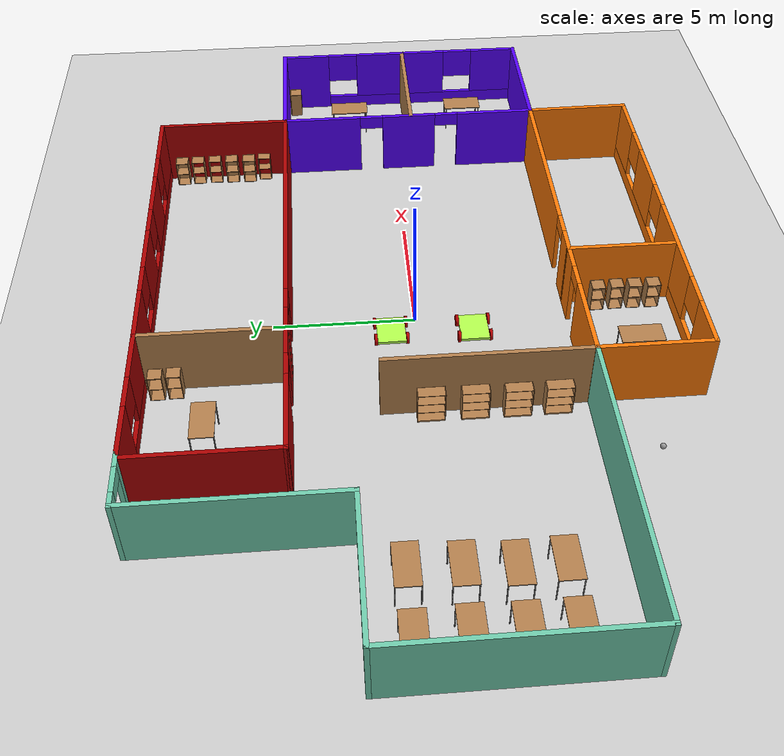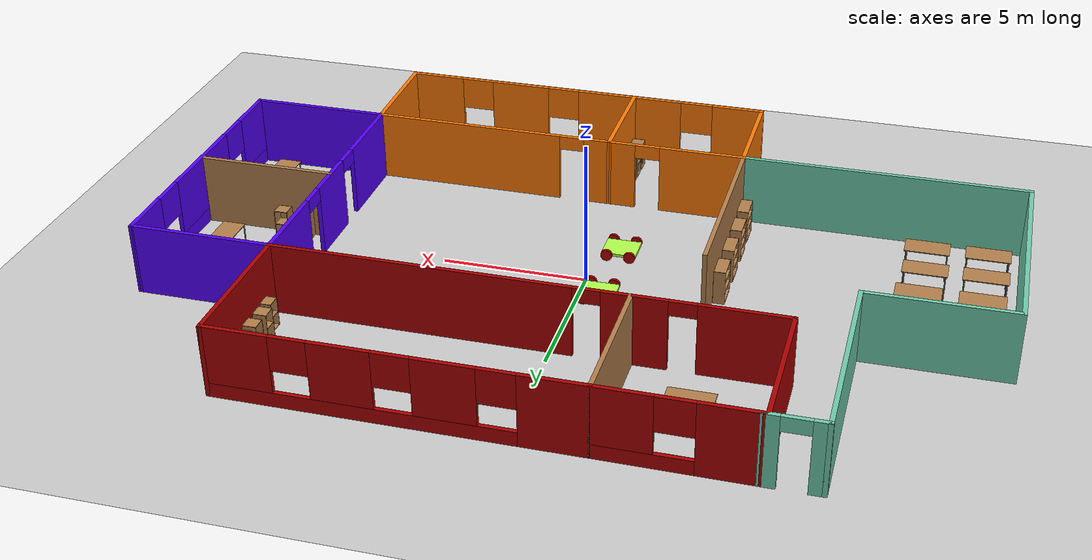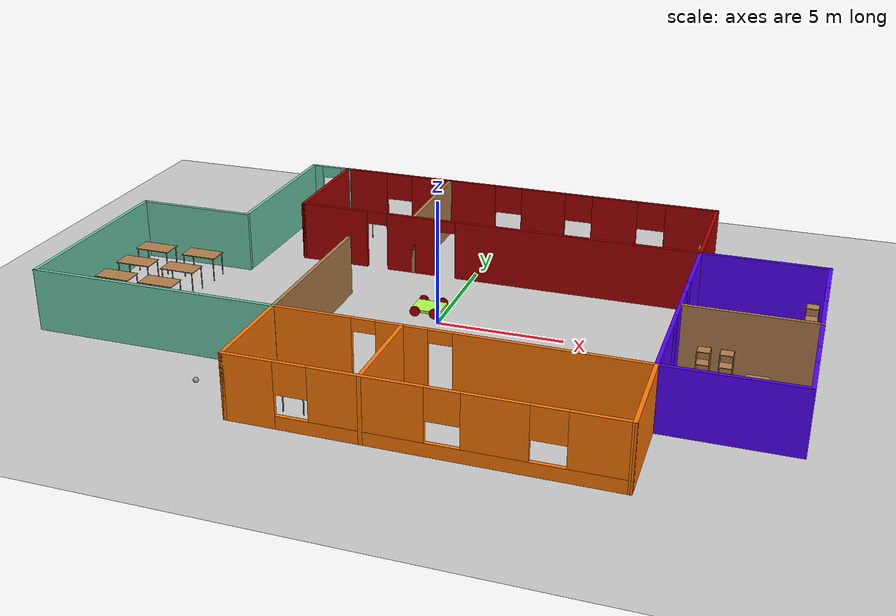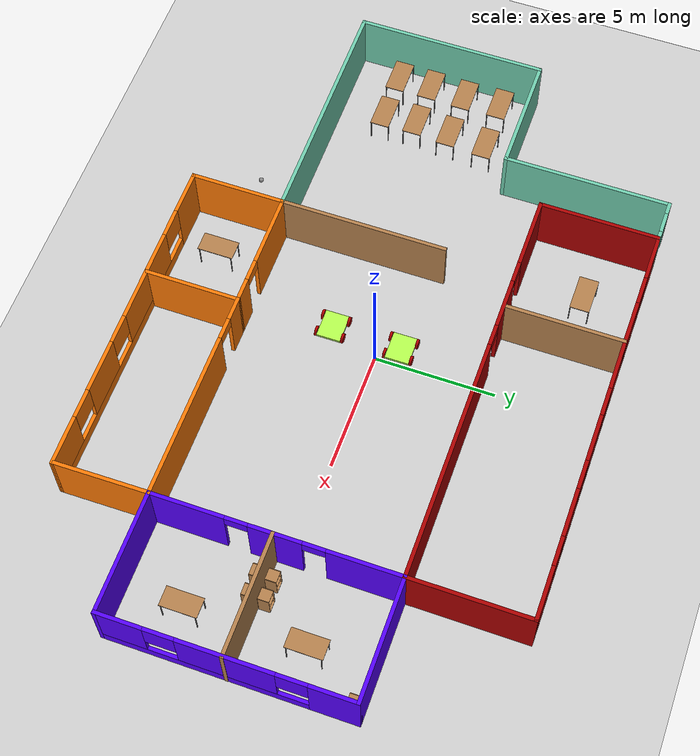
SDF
<sdf version="1.6">
 <world name="default">
  <plugin name="welcome" filename="libwelcome.so"/>
  <light name="sun" type="directional">
   <pose>0 0 10 0 -0 0</pose>
   <diffuse>0.8 0.8 0.8 1</diffuse>
   <specular>0.2 0.2 0.2 1</specular>
   <attenuation>
    <range>1000</range>
    <constant>0.9</constant>
    <linear>0.01</linear>
    <quadratic>0.001</quadratic>
   </attenuation>
   <direction>-0.5 0.1 -0.9</direction>
  </light>
  <model name="ground_plane">
   <static>1</static>
   <link name="link">
    <collision name="collision">
     <geometry><plane><normal>0 0 1</normal><size>100 100</size></plane></geometry>
     <surface>
      <contact><collide_bitmask>65535</collide_bitmask></contact>
      <friction><ode><mu>100</mu><mu2>50</mu2></ode></friction>
     </surface>
    </collision>
    <visual name="visual">
     <cast_shadows>0</cast_shadows>
     <geometry><plane><normal>0 0 1</normal><size>100 100</size></plane></geometry>
     <material>
      <script><uri>file://media/materials/scripts/gazebo.material</uri><name>Gazebo/Grey</name></script>
     </material>
    </visual>
   </link>
  </model>
  <gravity>0 0 -9.8</gravity>
  <magnetic_field>6e-06 2.3e-05 -4.2e-05</magnetic_field>
  <atmosphere type="adiabatic"/>
  <physics name="default_physics" default="0" type="ode">
   <max_step_size>0.001</max_step_size>
   <real_time_factor>1</real_time_factor>
   <real_time_update_rate>1000</real_time_update_rate>
  </physics>
  <scene><ambient>0.4 0.4 0.4 1</ambient><background>0.7 0.7 0.7 1</background><shadows>1</shadows></scene>
  <spherical_coordinates>
   <surface_model>EARTH_WGS84</surface_model>
   <latitude_deg>0</latitude_deg>
   <longitude_deg>0</longitude_deg>
   <elevation>0</elevation>
   <heading_deg>0</heading_deg>
  </spherical_coordinates>
  <model name="Building">
   <link name="Wall_10">
    <collision name="Wall_10_Collision">
     <geometry><box><size>5 0.15 2.5</size></box></geometry>
     <pose>0 0 1.25 0 -0 0</pose>
    </collision>
    <visual name="Wall_10_Visual">
     <pose>0 0 1.25 0 -0 0</pose>
     <geometry><box><size>5 0.15 2.5</size></box></geometry>
     <material>
      <script><uri>file://media/materials/scripts/gazebo.material</uri><name>Gazebo/Grey</name></script>
      <ambient>0.666667 0 0 1</ambient>
     </material>
     <meta><layer>0</layer></meta>
    </visual>
    <pose>9.27018 6.82319 0 0 0 -1.5708</pose>
   </link>
   <link name="Wall_11">
    <collision name="Wall_11_Collision">
     <geometry><box><size>5 0.15 2.5</size></box></geometry>
     <pose>0 0 1.25 0 -0 0</pose>
    </collision>
    <visual name="Wall_11_Visual">
     <pose>0 0 1.25 0 -0 0</pose>
     <geometry><box><size>5 0.15 2.5</size></box></geometry>
     <material>
      <script><uri>file://media/materials/scripts/gazebo.material</uri><name>Gazebo/Grey</name></script>
      <ambient>0.333333 0 1 1</ambient>
     </material>
     <meta><layer>0</layer></meta>
    </visual>
    <pose>11.6952 4.39843 0 0 -0 9.8e-05</pose>
   </link>
   <link name="Wall_12">
    <pose>14.1202 -0.52633 0 0 0 -1.5708</pose>
    <visual name="Wall_12_Visual_0">
     <pose>-4.03442 0 1.25 0 -0 0</pose>
     <geometry><box><size>1.93115 0.15 2.5</size></box></geometry>
     <material>
      <script><uri>file://media/materials/scripts/gazebo.material</uri><name>Gazebo/Grey</name></script>
      <ambient>0.333333 0 1 1</ambient>
     </material>
     <meta><layer>0</layer></meta>
    </visual>
    <collision name="Wall_12_Collision_0">
     <geometry><box><size>1.93115 0.15 2.5</size></box></geometry>
     <pose>-4.03442 0 1.25 0 -0 0</pose>
    </collision>
    <visual name="Wall_12_Visual_1">
     <pose>0.965577 0 0.25 0 -0 0</pose>
     <geometry><box><size>8.06885 0.15 0.5</size></box></geometry>
     <material>
      <script><uri>file://media/materials/scripts/gazebo.material</uri><name>Gazebo/Grey</name></script>
      <ambient>0.333333 0 1 1</ambient>
     </material>
     <meta><layer>0</layer></meta>
    </visual>
    <collision name="Wall_12_Collision_1">
     <geometry><box><size>8.06885 0.15 0.5</size></box></geometry>
     <pose>0.965577 0 0.25 0 -0 0</pose>
    </collision>
    <visual name="Wall_12_Visual_2">
     <pose>0.015256 0 1.5 0 -0 0</pose>
     <geometry><box><size>3.7682 0.15 2</size></box></geometry>
     <material>
      <script><uri>file://media/materials/scripts/gazebo.material</uri><name>Gazebo/Grey</name></script>
      <ambient>0.333333 0 1 1</ambient>
     </material>
     <meta><layer>0</layer></meta>
    </visual>
    <collision name="Wall_12_Collision_2">
     <geometry><box><size>3.7682 0.15 2</size></box></geometry>
     <pose>0.015256 0 1.5 0 -0 0</pose>
    </collision>
    <visual name="Wall_12_Visual_3">
     <pose>4.04968 0 1.5 0 -0 0</pose>
     <geometry><box><size>1.90064 0.15 2</size></box></geometry>
     <material>
      <script><uri>file://media/materials/scripts/gazebo.material</uri><name>Gazebo/Grey</name></script>
      <ambient>0.333333 0 1 1</ambient>
     </material>
     <meta><layer>0</layer></meta>
    </visual>
    <collision name="Wall_12_Collision_3">
     <geometry><box><size>1.90064 0.15 2</size></box></geometry>
     <pose>4.04968 0 1.5 0 -0 0</pose>
    </collision>
    <visual name="Wall_12_Visual_4">
     <pose>-2.46885 0 1.9 0 -0 0</pose>
     <geometry><box><size>1.2 0.15 1.2</size></box></geometry>
     <material>
      <script><uri>file://media/materials/scripts/gazebo.material</uri><name>Gazebo/Grey</name></script>
      <ambient>0.333333 0 1 1</ambient>
     </material>
     <meta><layer>0</layer></meta>
    </visual>
    <collision name="Wall_12_Collision_4">
     <geometry><box><size>1.2 0.15 1.2</size></box></geometry>
     <pose>-2.46885 0 1.9 0 -0 0</pose>
    </collision>
    <visual name="Wall_12_Visual_5">
     <pose>2.49936 0 1.9 0 -0 0</pose>
     <geometry><box><size>1.2 0.15 1.2</size></box></geometry>
     <material>
      <script><uri>file://media/materials/scripts/gazebo.material</uri><name>Gazebo/Grey</name></script>
      <ambient>0.333333 0 1 1</ambient>
     </material>
     <meta><layer>0</layer></meta>
    </visual>
    <collision name="Wall_12_Collision_5">
     <geometry><box><size>1.2 0.15 1.2</size></box></geometry>
     <pose>2.49936 0 1.9 0 -0 0</pose>
    </collision>
   </link>
   <link name="Wall_13">
    <collision name="Wall_13_Collision">
     <geometry><box><size>5 0.15 2.5</size></box></geometry>
     <pose>0 0 1.25 0 -0 0</pose>
    </collision>
    <visual name="Wall_13_Visual">
     <pose>0 0 1.25 0 -0 0</pose>
     <geometry><box><size>5 0.15 2.5</size></box></geometry>
     <material>
      <script><uri>file://media/materials/scripts/gazebo.material</uri><name>Gazebo/Grey</name></script>
      <ambient>0.333333 0 1 1</ambient>
     </material>
     <meta><layer>0</layer></meta>
    </visual>
    <pose>11.6952 -5.45133 0 0 -0 3.14159</pose>
   </link>
   <link name="Wall_15">
    <collision name="Wall_15_Collision">
     <geometry><box><size>5 0.15 2.5</size></box></geometry>
     <pose>0 0 1.25 0 -0 0</pose>
    </collision>
    <visual name="Wall_15_Visual">
     <pose>0 0 1.25 0 -0 0</pose>
     <geometry><box><size>5 0.15 2.5</size></box></geometry>
     <material>
      <script><uri>file://media/materials/scripts/gazebo.material</uri><name>Gazebo/Grey</name></script>
      <ambient>0.666667 0 0 1</ambient>
     </material>
     <meta><layer>0</layer></meta>
    </visual>
    <pose>-7.57982 6.82319 0 0 0 -1.5708</pose>
   </link>
   <link name="Wall_17">
    <pose>0.845177 4.39819 0 0 -0 0</pose>
    <visual name="Wall_17_Visual_0">
     <pose>-6.99749 0 1.25 0 -0 0</pose>
     <geometry><box><size>3.00503 0.15 2.5</size></box></geometry>
     <material>
      <script><uri>file://media/materials/scripts/gazebo.material</uri><name>Gazebo/Grey</name></script>
      <ambient>0.666667 0 0 1</ambient>
     </material>
     <meta><layer>0</layer></meta>
    </visual>
    <collision name="Wall_17_Collision_0">
     <geometry><box><size>3.00503 0.15 2.5</size></box></geometry>
     <pose>-6.99749 0 1.25 0 -0 0</pose>
    </collision>
    <visual name="Wall_17_Visual_1">
     <pose>-3.538 0 1.25 0 -0 0</pose>
     <geometry><box><size>2.11394 0.15 2.5</size></box></geometry>
     <material>
      <script><uri>file://media/materials/scripts/gazebo.material</uri><name>Gazebo/Grey</name></script>
      <ambient>0.666667 0 0 1</ambient>
     </material>
     <meta><layer>0</layer></meta>
    </visual>
    <collision name="Wall_17_Collision_1">
     <geometry><box><size>2.11394 0.15 2.5</size></box></geometry>
     <pose>-3.538 0 1.25 0 -0 0</pose>
    </collision>
    <visual name="Wall_17_Visual_2">
     <pose>3.45948 0 1.25 0 -0 0</pose>
     <geometry><box><size>10.081 0.15 2.5</size></box></geometry>
     <material>
      <script><uri>file://media/materials/scripts/gazebo.material</uri><name>Gazebo/Grey</name></script>
      <ambient>0.666667 0 0 1</ambient>
     </material>
     <meta><layer>0</layer></meta>
    </visual>
    <collision name="Wall_17_Collision_2">
     <geometry><box><size>10.081 0.15 2.5</size></box></geometry>
     <pose>3.45948 0 1.25 0 -0 0</pose>
    </collision>
    <visual name="Wall_17_Visual_3">
     <pose>-5.04497 0 2.25 0 -0 0</pose>
     <geometry><box><size>0.9 0.15 0.5</size></box></geometry>
     <material>
      <script><uri>file://media/materials/scripts/gazebo.material</uri><name>Gazebo/Grey</name></script>
      <ambient>0.666667 0 0 1</ambient>
     </material>
     <meta><layer>0</layer></meta>
    </visual>
    <collision name="Wall_17_Collision_3">
     <geometry><box><size>0.9 0.15 0.5</size></box></geometry>
     <pose>-5.04497 0 2.25 0 -0 0</pose>
    </collision>
    <visual name="Wall_17_Visual_4">
     <pose>-2.03103 0 2.25 0 -0 0</pose>
     <geometry><box><size>0.9 0.15 0.5</size></box></geometry>
     <material>
      <script><uri>file://media/materials/scripts/gazebo.material</uri><name>Gazebo/Grey</name></script>
      <ambient>0.666667 0 0 1</ambient>
     </material>
     <meta><layer>0</layer></meta>
    </visual>
    <collision name="Wall_17_Collision_4">
     <geometry><box><size>0.9 0.15 0.5</size></box></geometry>
     <pose>-2.03103 0 2.25 0 -0 0</pose>
    </collision>
   </link>
   <link name="Wall_19">
    <collision name="Wall_19_Collision">
     <geometry><box><size>5 0.15 2.5</size></box></geometry>
     <pose>0 0 1.25 0 -0 0</pose>
    </collision>
    <visual name="Wall_19_Visual">
     <pose>0 0 1.25 0 -0 0</pose>
     <geometry><box><size>5 0.15 2.5</size></box></geometry>
     <material>
      <script><uri>file://media/materials/scripts/gazebo.material</uri><name>Gazebo/Wood</name></script>
      <ambient>0.666667 0 0 1</ambient>
     </material>
     <meta><layer>0</layer></meta>
    </visual>
    <pose>-2.57982 6.82319 0 0 0 -1.5708</pose>
   </link>
   <link name="Wall_22">
    <collision name="Wall_22_Collision">
     <geometry><box><size>7 0.15 2.5</size></box></geometry>
     <pose>0 0 1.25 0 -0 0</pose>
    </collision>
    <visual name="Wall_22_Visual">
     <pose>0 0 1.25 0 -0 0</pose>
     <geometry><box><size>7 0.15 2.5</size></box></geometry>
     <material>
      <script><uri>file://media/materials/scripts/gazebo.material</uri><name>Gazebo/Grey</name></script>
      <ambient>0.435294 0.796078 0.67451 1</ambient>
     </material>
     <meta><layer>0</layer></meta>
    </visual>
    <pose>-9.27982 5.84632 0 0 0 -1.5708</pose>
   </link>
   <link name="Wall_23">
    <collision name="Wall_23_Collision">
     <geometry><box><size>5 0.15 2.5</size></box></geometry>
     <pose>0 0 1.25 0 -0 0</pose>
    </collision>
    <visual name="Wall_23_Visual">
     <pose>0 0 1.25 0 -0 0</pose>
     <geometry><box><size>5 0.15 2.5</size></box></geometry>
     <material>
      <script><uri>file://media/materials/scripts/gazebo.material</uri><name>Gazebo/Grey</name></script>
      <ambient>0.435294 0.796078 0.67451 1</ambient>
     </material>
     <meta><layer>0</layer></meta>
    </visual>
    <pose>-11.7048 2.42132 0 0 -0 3.14159</pose>
   </link>
   <link name="Wall_24">
    <collision name="Wall_24_Collision">
     <geometry><box><size>8 0.15 2.5</size></box></geometry>
     <pose>0 0 1.25 0 -0 0</pose>
    </collision>
    <visual name="Wall_24_Visual">
     <pose>0 0 1.25 0 -0 0</pose>
     <geometry><box><size>8 0.15 2.5</size></box></geometry>
     <material>
      <script><uri>file://media/materials/scripts/gazebo.material</uri><name>Gazebo/Grey</name></script>
      <ambient>0.435294 0.796078 0.67451 1</ambient>
     </material>
     <meta><layer>0</layer></meta>
    </visual>
    <pose>-14.1298 -1.50368 0 0 0 -1.5708</pose>
   </link>
   <link name="Wall_25">
    <collision name="Wall_25_Collision">
     <geometry><box><size>10 0.15 2.5</size></box></geometry>
     <pose>0 0 1.25 0 -0 0</pose>
    </collision>
    <visual name="Wall_25_Visual">
     <pose>0 0 1.25 0 -0 0</pose>
     <geometry><box><size>10 0.15 2.5</size></box></geometry>
     <material>
      <script><uri>file://media/materials/scripts/gazebo.material</uri><name>Gazebo/Grey</name></script>
      <ambient>0.435294 0.796078 0.67451 1</ambient>
     </material>
     <meta><layer>0</layer></meta>
    </visual>
    <pose>-9.20482 -5.42868 0 0 -0 0</pose>
   </link>
   <link name="Wall_28">
    <collision name="Wall_28_Collision">
     <geometry><box><size>7 0.15 2.5</size></box></geometry>
     <pose>0 0 1.25 0 -0 0</pose>
    </collision>
    <visual name="Wall_28_Visual">
     <pose>0 0 1.25 0 -0 0</pose>
     <geometry><box><size>7 0.15 2.5</size></box></geometry>
     <material>
      <script><uri>file://media/materials/scripts/gazebo.material</uri><name>Gazebo/Wood</name></script>
      <ambient>1 1 1 1</ambient>
     </material>
     <meta><layer>0</layer></meta>
    </visual>
    <pose>-4.28105 -1.99466 0 0 -0 1.5708</pose>
   </link>
   <link name="Wall_30">
    <pose>9.27018 -0.526806 0 0 0 -1.5708</pose>
    <visual name="Wall_30_Visual_0">
     <pose>-3.46998 0 1.25 0 -0 0</pose>
     <geometry><box><size>3.06003 0.15 2.5</size></box></geometry>
     <material>
      <script><uri>file://media/materials/scripts/gazebo.material</uri><name>Gazebo/Grey</name></script>
      <ambient>0.333333 0 1 1</ambient>
     </material>
     <meta><layer>0</layer></meta>
    </visual>
    <collision name="Wall_30_Collision_0">
     <geometry><box><size>3.06003 0.15 2.5</size></box></geometry>
     <pose>-3.46998 0 1.25 0 -0 0</pose>
    </collision>
    <visual name="Wall_30_Visual_1">
     <pose>0.01043 0 1.25 0 -0 0</pose>
     <geometry><box><size>2.10079 0.15 2.5</size></box></geometry>
     <material>
      <script><uri>file://media/materials/scripts/gazebo.material</uri><name>Gazebo/Grey</name></script>
      <ambient>0.333333 0 1 1</ambient>
     </material>
     <meta><layer>0</layer></meta>
    </visual>
    <collision name="Wall_30_Collision_1">
     <geometry><box><size>2.10079 0.15 2.5</size></box></geometry>
     <pose>0.01043 0 1.25 0 -0 0</pose>
    </collision>
    <visual name="Wall_30_Visual_2">
     <pose>3.48041 0 1.25 0 -0 0</pose>
     <geometry><box><size>3.03917 0.15 2.5</size></box></geometry>
     <material>
      <script><uri>file://media/materials/scripts/gazebo.material</uri><name>Gazebo/Grey</name></script>
      <ambient>0.333333 0 1 1</ambient>
     </material>
     <meta><layer>0</layer></meta>
    </visual>
    <collision name="Wall_30_Collision_2">
     <geometry><box><size>3.03917 0.15 2.5</size></box></geometry>
     <pose>3.48041 0 1.25 0 -0 0</pose>
    </collision>
    <visual name="Wall_30_Visual_3">
     <pose>-1.48997 0 2.25 0 -0 0</pose>
     <geometry><box><size>0.9 0.15 0.5</size></box></geometry>
     <material>
      <script><uri>file://media/materials/scripts/gazebo.material</uri><name>Gazebo/Grey</name></script>
      <ambient>0.333333 0 1 1</ambient>
     </material>
     <meta><layer>0</layer></meta>
    </visual>
    <collision name="Wall_30_Collision_3">
     <geometry><box><size>0.9 0.15 0.5</size></box></geometry>
     <pose>-1.48997 0 2.25 0 -0 0</pose>
    </collision>
    <visual name="Wall_30_Visual_4">
     <pose>1.51083 0 2.25 0 -0 0</pose>
     <geometry><box><size>0.9 0.15 0.5</size></box></geometry>
     <material>
      <script><uri>file://media/materials/scripts/gazebo.material</uri><name>Gazebo/Grey</name></script>
      <ambient>0.333333 0 1 1</ambient>
     </material>
     <meta><layer>0</layer></meta>
    </visual>
    <collision name="Wall_30_Collision_4">
     <geometry><box><size>0.9 0.15 0.5</size></box></geometry>
     <pose>1.51083 0 2.25 0 -0 0</pose>
    </collision>
   </link>
   <link name="Wall_32">
    <collision name="Wall_32_Collision">
     <geometry><box><size>5 0.15 2.5</size></box></geometry>
     <pose>0 0 1.25 0 -0 0</pose>
    </collision>
    <visual name="Wall_32_Visual">
     <pose>0 0 1.25 0 -0 0</pose>
     <geometry><box><size>5 0.15 2.5</size></box></geometry>
     <material>
      <script><uri>file://media/materials/scripts/gazebo.material</uri><name>Gazebo/Wood</name></script>
      <ambient>0.333333 0.333333 1 1</ambient>
     </material>
     <meta><layer>0</layer></meta>
    </visual>
    <pose>11.7048 -0.619519 0 0 -0 0</pose>
   </link>
   <link name="Wall_38">
    <collision name="Wall_38_Collision">
     <geometry><box><size>4 0.15 2.5</size></box></geometry>
     <pose>0 0 1.25 0 -0 0</pose>
    </collision>
    <visual name="Wall_38_Visual">
     <pose>0 0 1.25 0 -0 0</pose>
     <geometry><box><size>4 0.15 2.5</size></box></geometry>
     <material>
      <script><uri>file://media/materials/scripts/gazebo.material</uri><name>Gazebo/Grey</name></script>
      <ambient>0.996078 0.47451 0.0196078 1</ambient>
     </material>
     <meta><layer>0</layer></meta>
    </visual>
    <pose>-4.28105 -7.34466 0 0 0 -1.5708</pose>
   </link>
   <link name="Wall_39">
    <pose>2.51895 -9.26966 0 0 -0 0</pose>
    <visual name="Wall_39_Visual_0">
     <pose>-5.91598 0 1.25 0 -0 0</pose>
     <geometry><box><size>1.91805 0.15 2.5</size></box></geometry>
     <material>
      <script><uri>file://media/materials/scripts/gazebo.material</uri><name>Gazebo/Grey</name></script>
      <ambient>0.996078 0.47451 0.0196078 1</ambient>
     </material>
     <meta><layer>0</layer></meta>
    </visual>
    <collision name="Wall_39_Collision_0">
     <geometry><box><size>1.91805 0.15 2.5</size></box></geometry>
     <pose>-5.91598 0 1.25 0 -0 0</pose>
    </collision>
    <visual name="Wall_39_Visual_1">
     <pose>0.959024 0 0.25 0 -0 0</pose>
     <geometry><box><size>11.832 0.15 0.5</size></box></geometry>
     <material>
      <script><uri>file://media/materials/scripts/gazebo.material</uri><name>Gazebo/Grey</name></script>
      <ambient>0.996078 0.47451 0.0196078 1</ambient>
     </material>
     <meta><layer>0</layer></meta>
    </visual>
    <collision name="Wall_39_Collision_1">
     <geometry><box><size>11.832 0.15 0.5</size></box></geometry>
     <pose>0.959024 0 0.25 0 -0 0</pose>
    </collision>
    <visual name="Wall_39_Visual_2">
     <pose>-1.77131 0 1.5 0 -0 0</pose>
     <geometry><box><size>3.97128 0.15 2</size></box></geometry>
     <material>
      <script><uri>file://media/materials/scripts/gazebo.material</uri><name>Gazebo/Grey</name></script>
      <ambient>0.996078 0.47451 0.0196078 1</ambient>
     </material>
     <meta><layer>0</layer></meta>
    </visual>
    <collision name="Wall_39_Collision_2">
     <geometry><box><size>3.97128 0.15 2</size></box></geometry>
     <pose>-1.77131 0 1.5 0 -0 0</pose>
    </collision>
    <visual name="Wall_39_Visual_3">
     <pose>2.5205 0 1.5 0 -0 0</pose>
     <geometry><box><size>2.21234 0.15 2</size></box></geometry>
     <material>
      <script><uri>file://media/materials/scripts/gazebo.material</uri><name>Gazebo/Grey</name></script>
      <ambient>0.996078 0.47451 0.0196078 1</ambient>
     </material>
     <meta><layer>0</layer></meta>
    </visual>
    <collision name="Wall_39_Collision_3">
     <geometry><box><size>2.21234 0.15 2</size></box></geometry>
     <pose>2.5205 0 1.5 0 -0 0</pose>
    </collision>
    <visual name="Wall_39_Visual_4">
     <pose>5.85083 0 1.5 0 -0 0</pose>
     <geometry><box><size>2.04833 0.15 2</size></box></geometry>
     <material>
      <script><uri>file://media/materials/scripts/gazebo.material</uri><name>Gazebo/Grey</name></script>
      <ambient>0.996078 0.47451 0.0196078 1</ambient>
     </material>
     <meta><layer>0</layer></meta>
    </visual>
    <collision name="Wall_39_Collision_4">
     <geometry><box><size>2.04833 0.15 2</size></box></geometry>
     <pose>5.85083 0 1.5 0 -0 0</pose>
    </collision>
    <visual name="Wall_39_Visual_5">
     <pose>-4.35695 0 1.9 0 -0 0</pose>
     <geometry><box><size>1.2 0.15 1.2</size></box></geometry>
     <material>
      <script><uri>file://media/materials/scripts/gazebo.material</uri><name>Gazebo/Grey</name></script>
      <ambient>0.996078 0.47451 0.0196078 1</ambient>
     </material>
     <meta><layer>0</layer></meta>
    </visual>
    <collision name="Wall_39_Collision_5">
     <geometry><box><size>1.2 0.15 1.2</size></box></geometry>
     <pose>-4.35695 0 1.9 0 -0 0</pose>
    </collision>
    <visual name="Wall_39_Visual_6">
     <pose>0.814326 0 1.9 0 -0 0</pose>
     <geometry><box><size>1.2 0.15 1.2</size></box></geometry>
     <material>
      <script><uri>file://media/materials/scripts/gazebo.material</uri><name>Gazebo/Grey</name></script>
      <ambient>0.996078 0.47451 0.0196078 1</ambient>
     </material>
     <meta><layer>0</layer></meta>
    </visual>
    <collision name="Wall_39_Collision_6">
     <geometry><box><size>1.2 0.15 1.2</size></box></geometry>
     <pose>0.814326 0 1.9 0 -0 0</pose>
    </collision>
    <visual name="Wall_39_Visual_7">
     <pose>4.22667 0 1.9 0 -0 0</pose>
     <geometry><box><size>1.2 0.15 1.2</size></box></geometry>
     <material>
      <script><uri>file://media/materials/scripts/gazebo.material</uri><name>Gazebo/Grey</name></script>
      <ambient>0.996078 0.47451 0.0196078 1</ambient>
     </material>
     <meta><layer>0</layer></meta>
    </visual>
    <collision name="Wall_39_Collision_7">
     <geometry><box><size>1.2 0.15 1.2</size></box></geometry>
     <pose>4.22667 0 1.9 0 -0 0</pose>
    </collision>
   </link>
   <link name="Wall_40">
    <collision name="Wall_40_Collision">
     <geometry><box><size>3.96816 0.15 2.5</size></box></geometry>
     <pose>0 0 1.25 0 -0 0</pose>
    </collision>
    <visual name="Wall_40_Visual">
     <pose>0 0 1.25 0 -0 0</pose>
     <geometry><box><size>3.96816 0.15 2.5</size></box></geometry>
     <material>
      <script><uri>file://media/materials/scripts/gazebo.material</uri><name>Gazebo/Grey</name></script>
      <ambient>0.996078 0.47451 0.0196078 1</ambient>
     </material>
     <meta><layer>0</layer></meta>
    </visual>
    <pose>9.29456 -7.36073 0 0 -0 1.58357</pose>
   </link>
   <link name="Wall_42">
    <pose>-1.85605 -5.41965 0 0 -0 0</pose>
    <visual name="Wall_42_Visual_0">
     <pose>-0.965225 0 1.25 0 -0 0</pose>
     <geometry><box><size>3.06955 0.15 2.5</size></box></geometry>
     <material>
      <script><uri>file://media/materials/scripts/gazebo.material</uri><name>Gazebo/Grey</name></script>
      <ambient>0.996078 0.47451 0.0196078 1</ambient>
     </material>
     <meta><layer>0</layer></meta>
    </visual>
    <collision name="Wall_42_Collision_0">
     <geometry><box><size>3.06955 0.15 2.5</size></box></geometry>
     <pose>-0.965225 0 1.25 0 -0 0</pose>
    </collision>
    <visual name="Wall_42_Visual_1">
     <pose>1.98477 0 1.25 0 -0 0</pose>
     <geometry><box><size>1.03045 0.15 2.5</size></box></geometry>
     <material>
      <script><uri>file://media/materials/scripts/gazebo.material</uri><name>Gazebo/Grey</name></script>
      <ambient>0.996078 0.47451 0.0196078 1</ambient>
     </material>
     <meta><layer>0</layer></meta>
    </visual>
    <collision name="Wall_42_Collision_1">
     <geometry><box><size>1.03045 0.15 2.5</size></box></geometry>
     <pose>1.98477 0 1.25 0 -0 0</pose>
    </collision>
    <visual name="Wall_42_Visual_2">
     <pose>1.01955 0 2.25 0 -0 0</pose>
     <geometry><box><size>0.9 0.15 0.5</size></box></geometry>
     <material>
      <script><uri>file://media/materials/scripts/gazebo.material</uri><name>Gazebo/Grey</name></script>
      <ambient>0.996078 0.47451 0.0196078 1</ambient>
     </material>
     <meta><layer>0</layer></meta>
    </visual>
    <collision name="Wall_42_Collision_2">
     <geometry><box><size>0.9 0.15 0.5</size></box></geometry>
     <pose>1.01955 0 2.25 0 -0 0</pose>
    </collision>
   </link>
   <link name="Wall_43">
    <pose>4.91956 -5.43573 0 0 0 -0.003695</pose>
    <visual name="Wall_43_Visual_0">
     <pose>-3.91633 0 1.25 0 -0 0</pose>
     <geometry><box><size>1.01862 0.15 2.5</size></box></geometry>
     <material>
      <script><uri>file://media/materials/scripts/gazebo.material</uri><name>Gazebo/Grey</name></script>
      <ambient>0.996078 0.47451 0.0196078 1</ambient>
     </material>
     <meta><layer>0</layer></meta>
    </visual>
    <collision name="Wall_43_Collision_0">
     <geometry><box><size>1.01862 0.15 2.5</size></box></geometry>
     <pose>-3.91633 0 1.25 0 -0 0</pose>
    </collision>
    <visual name="Wall_43_Visual_1">
     <pose>0.959309 0 1.25 0 -0 0</pose>
     <geometry><box><size>6.93267 0.15 2.5</size></box></geometry>
     <material>
      <script><uri>file://media/materials/scripts/gazebo.material</uri><name>Gazebo/Grey</name></script>
      <ambient>0.996078 0.47451 0.0196078 1</ambient>
     </material>
     <meta><layer>0</layer></meta>
    </visual>
    <collision name="Wall_43_Collision_1">
     <geometry><box><size>6.93267 0.15 2.5</size></box></geometry>
     <pose>0.959309 0 1.25 0 -0 0</pose>
    </collision>
    <visual name="Wall_43_Visual_2">
     <pose>-2.95702 0 2.25 0 -0 0</pose>
     <geometry><box><size>0.9 0.15 0.5</size></box></geometry>
     <material>
      <script><uri>file://media/materials/scripts/gazebo.material</uri><name>Gazebo/Grey</name></script>
      <ambient>0.996078 0.47451 0.0196078 1</ambient>
     </material>
     <meta><layer>0</layer></meta>
    </visual>
    <collision name="Wall_43_Collision_2">
     <geometry><box><size>0.9 0.15 0.5</size></box></geometry>
     <pose>-2.95702 0 2.25 0 -0 0</pose>
    </collision>
   </link>
   <link name="Wall_45">
    <collision name="Wall_45_Collision">
     <geometry><box><size>4 0.15 2.5</size></box></geometry>
     <pose>0 0 1.25 0 -0 0</pose>
    </collision>
    <visual name="Wall_45_Visual">
     <pose>0 0 1.25 0 -0 0</pose>
     <geometry><box><size>4 0.15 2.5</size></box></geometry>
     <material>
      <script><uri>file://media/materials/scripts/gazebo.material</uri><name>Gazebo/Grey</name></script>
      <ambient>0.996078 0.47451 0.0196078 1</ambient>
     </material>
     <meta><layer>0</layer></meta>
    </visual>
    <pose>0.574364 -7.34668 0 0 0 -1.5708</pose>
   </link>
   <link name="Wall_7">
    <pose>-8.35482 9.27132 0 0 -0 0</pose>
    <visual name="Wall_7_Visual_0">
     <pose>-0.727539 0 1.25 0 -0 0</pose>
     <geometry><box><size>0.544922 0.15 2.5</size></box></geometry>
     <material>
      <script><uri>file://media/materials/scripts/gazebo.material</uri><name>Gazebo/Grey</name></script>
      <ambient>0.435294 0.796078 0.67451 1</ambient>
     </material>
     <meta><layer>0</layer></meta>
    </visual>
    <collision name="Wall_7_Collision_0">
     <geometry><box><size>0.544922 0.15 2.5</size></box></geometry>
     <pose>-0.727539 0 1.25 0 -0 0</pose>
    </collision>
    <visual name="Wall_7_Visual_1">
     <pose>0.722461 0 1.25 0 -0 0</pose>
     <geometry><box><size>0.555078 0.15 2.5</size></box></geometry>
     <material>
      <script><uri>file://media/materials/scripts/gazebo.material</uri><name>Gazebo/Grey</name></script>
      <ambient>0.435294 0.796078 0.67451 1</ambient>
     </material>
     <meta><layer>0</layer></meta>
    </visual>
    <collision name="Wall_7_Collision_1">
     <geometry><box><size>0.555078 0.15 2.5</size></box></geometry>
     <pose>0.722461 0 1.25 0 -0 0</pose>
    </collision>
    <visual name="Wall_7_Visual_2">
     <pose>-0.005078 0 2.25 0 -0 0</pose>
     <geometry><box><size>0.9 0.15 0.5</size></box></geometry>
     <material>
      <script><uri>file://media/materials/scripts/gazebo.material</uri><name>Gazebo/Grey</name></script>
      <ambient>0.435294 0.796078 0.67451 1</ambient>
     </material>
     <meta><layer>0</layer></meta>
    </visual>
    <collision name="Wall_7_Collision_2">
     <geometry><box><size>0.9 0.15 0.5</size></box></geometry>
     <pose>-0.005078 0 2.25 0 -0 0</pose>
    </collision>
   </link>
   <link name="Wall_8">
    <pose>-5.00482 9.25976 0 0 0 -0.004769</pose>
    <visual name="Wall_8_Visual_0">
     <pose>-1.55185 0 1.25 0 -0 0</pose>
     <geometry><box><size>1.8963 0.15 2.5</size></box></geometry>
     <material>
      <script><uri>file://media/materials/scripts/gazebo.material</uri><name>Gazebo/Grey</name></script>
      <ambient>0.666667 0 0 1</ambient>
     </material>
     <meta><layer>0</layer></meta>
    </visual>
    <collision name="Wall_8_Collision_0">
     <geometry><box><size>1.8963 0.15 2.5</size></box></geometry>
     <pose>-1.55185 0 1.25 0 -0 0</pose>
    </collision>
    <visual name="Wall_8_Visual_1">
     <pose>0.948148 0 0.25 0 -0 0</pose>
     <geometry><box><size>3.10371 0.15 0.5</size></box></geometry>
     <material>
      <script><uri>file://media/materials/scripts/gazebo.material</uri><name>Gazebo/Grey</name></script>
      <ambient>0.666667 0 0 1</ambient>
     </material>
     <meta><layer>0</layer></meta>
    </visual>
    <collision name="Wall_8_Collision_1">
     <geometry><box><size>3.10371 0.15 0.5</size></box></geometry>
     <pose>0.948148 0 0.25 0 -0 0</pose>
    </collision>
    <visual name="Wall_8_Visual_2">
     <pose>1.54815 0 1.5 0 -0 0</pose>
     <geometry><box><size>1.9037 0.15 2</size></box></geometry>
     <material>
      <script><uri>file://media/materials/scripts/gazebo.material</uri><name>Gazebo/Grey</name></script>
      <ambient>0.666667 0 0 1</ambient>
     </material>
     <meta><layer>0</layer></meta>
    </visual>
    <collision name="Wall_8_Collision_2">
     <geometry><box><size>1.9037 0.15 2</size></box></geometry>
     <pose>1.54815 0 1.5 0 -0 0</pose>
    </collision>
    <visual name="Wall_8_Visual_3">
     <pose>-0.003705 0 1.9 0 -0 0</pose>
     <geometry><box><size>1.2 0.15 1.2</size></box></geometry>
     <material>
      <script><uri>file://media/materials/scripts/gazebo.material</uri><name>Gazebo/Grey</name></script>
      <ambient>0.666667 0 0 1</ambient>
     </material>
     <meta><layer>0</layer></meta>
    </visual>
    <collision name="Wall_8_Collision_3">
     <geometry><box><size>1.2 0.15 1.2</size></box></geometry>
     <pose>-0.003705 0 1.9 0 -0 0</pose>
    </collision>
   </link>
   <link name="Wall_9">
    <pose>3.34518 9.24819 0 0 -0 0</pose>
    <visual name="Wall_9_Visual_0">
     <pose>-4.89214 0 1.25 0 -0 0</pose>
     <geometry><box><size>2.21571 0.15 2.5</size></box></geometry>
     <material>
      <script><uri>file://media/materials/scripts/gazebo.material</uri><name>Gazebo/Grey</name></script>
      <ambient>0.666667 0 0 1</ambient>
     </material>
     <meta><layer>0</layer></meta>
    </visual>
    <collision name="Wall_9_Collision_0">
     <geometry><box><size>2.21571 0.15 2.5</size></box></geometry>
     <pose>-4.89214 0 1.25 0 -0 0</pose>
    </collision>
    <visual name="Wall_9_Visual_1">
     <pose>1.10786 0 0.25 0 -0 0</pose>
     <geometry><box><size>9.78429 0.15 0.5</size></box></geometry>
     <material>
      <script><uri>file://media/materials/scripts/gazebo.material</uri><name>Gazebo/Grey</name></script>
      <ambient>0.666667 0 0 1</ambient>
     </material>
     <meta><layer>0</layer></meta>
    </visual>
    <collision name="Wall_9_Collision_1">
     <geometry><box><size>9.78429 0.15 0.5</size></box></geometry>
     <pose>1.10786 0 0.25 0 -0 0</pose>
    </collision>
    <visual name="Wall_9_Visual_2">
     <pose>-1.59359 0 1.5 0 -0 0</pose>
     <geometry><box><size>1.98138 0.15 2</size></box></geometry>
     <material>
      <script><uri>file://media/materials/scripts/gazebo.material</uri><name>Gazebo/Grey</name></script>
      <ambient>0.666667 0 0 1</ambient>
     </material>
     <meta><layer>0</layer></meta>
    </visual>
    <collision name="Wall_9_Collision_2">
     <geometry><box><size>1.98138 0.15 2</size></box></geometry>
     <pose>-1.59359 0 1.5 0 -0 0</pose>
    </collision>
    <visual name="Wall_9_Visual_3">
     <pose>1.58779 0 1.5 0 -0 0</pose>
     <geometry><box><size>1.98138 0.15 2</size></box></geometry>
     <material>
      <script><uri>file://media/materials/scripts/gazebo.material</uri><name>Gazebo/Grey</name></script>
      <ambient>0.666667 0 0 1</ambient>
     </material>
     <meta><layer>0</layer></meta>
    </visual>
    <collision name="Wall_9_Collision_3">
     <geometry><box><size>1.98138 0.15 2</size></box></geometry>
     <pose>1.58779 0 1.5 0 -0 0</pose>
    </collision>
    <visual name="Wall_9_Visual_4">
     <pose>4.88924 0 1.5 0 -0 0</pose>
     <geometry><box><size>2.22152 0.15 2</size></box></geometry>
     <material>
      <script><uri>file://media/materials/scripts/gazebo.material</uri><name>Gazebo/Grey</name></script>
      <ambient>0.666667 0 0 1</ambient>
     </material>
     <meta><layer>0</layer></meta>
    </visual>
    <collision name="Wall_9_Collision_4">
     <geometry><box><size>2.22152 0.15 2</size></box></geometry>
     <pose>4.88924 0 1.5 0 -0 0</pose>
    </collision>
    <visual name="Wall_9_Visual_5">
     <pose>-3.18429 0 1.9 0 -0 0</pose>
     <geometry><box><size>1.2 0.15 1.2</size></box></geometry>
     <material>
      <script><uri>file://media/materials/scripts/gazebo.material</uri><name>Gazebo/Grey</name></script>
      <ambient>0.666667 0 0 1</ambient>
     </material>
     <meta><layer>0</layer></meta>
    </visual>
    <collision name="Wall_9_Collision_5">
     <geometry><box><size>1.2 0.15 1.2</size></box></geometry>
     <pose>-3.18429 0 1.9 0 -0 0</pose>
    </collision>
    <visual name="Wall_9_Visual_6">
     <pose>-0.002902 0 1.9 0 -0 0</pose>
     <geometry><box><size>1.2 0.15 1.2</size></box></geometry>
     <material>
      <script><uri>file://media/materials/scripts/gazebo.material</uri><name>Gazebo/Grey</name></script>
      <ambient>0.666667 0 0 1</ambient>
     </material>
     <meta><layer>0</layer></meta>
    </visual>
    <collision name="Wall_9_Collision_6">
     <geometry><box><size>1.2 0.15 1.2</size></box></geometry>
     <pose>-0.002902 0 1.9 0 -0 0</pose>
    </collision>
    <visual name="Wall_9_Visual_7">
     <pose>3.17848 0 1.9 0 -0 0</pose>
     <geometry><box><size>1.2 0.15 1.2</size></box></geometry>
     <material>
      <script><uri>file://media/materials/scripts/gazebo.material</uri><name>Gazebo/Grey</name></script>
      <ambient>0.666667 0 0 1</ambient>
     </material>
     <meta><layer>0</layer></meta>
    </visual>
    <collision name="Wall_9_Collision_7">
     <geometry><box><size>1.2 0.15 1.2</size></box></geometry>
     <pose>3.17848 0 1.9 0 -0 0</pose>
    </collision>
   </link>
   <static>1</static>
  </model>
  <model name="bookshelf">
   <static>1</static>
   <link name="link">
    <inertial><mass>1</mass></inertial>
    <collision name="back">
     <pose>0 0.005 0.6 0 -0 0</pose>
     <geometry><box><size>0.9 0.01 1.2</size></box></geometry>
    </collision>
    <visual name="visual1">
     <pose>0 0.005 0.6 0 -0 0</pose>
     <geometry><box><size>0.9 0.01 1.2</size></box></geometry>
     <material>
      <script><uri>file://media/materials/scripts/gazebo.material</uri><name>Gazebo/Wood</name></script>
     </material>
    </visual>
    <collision name="left_side">
     <pose>0.45 -0.195 0.6 0 -0 0</pose>
     <geometry><box><size>0.02 0.4 1.2</size></box></geometry>
    </collision>
    <visual name="visual2">
     <pose>0.45 -0.195 0.6 0 -0 0</pose>
     <geometry><box><size>0.02 0.4 1.2</size></box></geometry>
     <material>
      <script><uri>file://media/materials/scripts/gazebo.material</uri><name>Gazebo/Wood</name></script>
     </material>
    </visual>
    <collision name="right_side">
     <pose>-0.45 -0.195 0.6 0 -0 0</pose>
     <geometry><box><size>0.02 0.4 1.2</size></box></geometry>
    </collision>
    <visual name="visual3">
     <pose>-0.45 -0.195 0.6 0 -0 0</pose>
     <geometry><box><size>0.02 0.4 1.2</size></box></geometry>
     <material>
      <script><uri>file://media/materials/scripts/gazebo.material</uri><name>Gazebo/Wood</name></script>
     </material>
    </visual>
    <collision name="bottom">
     <pose>0 -0.195 0.03 0 -0 0</pose>
     <geometry><box><size>0.88 0.4 0.06</size></box></geometry>
    </collision>
    <visual name="visual4">
     <pose>0 -0.195 0.03 0 -0 0</pose>
     <geometry><box><size>0.88 0.4 0.06</size></box></geometry>
     <material>
      <script><uri>file://media/materials/scripts/gazebo.material</uri><name>Gazebo/Wood</name></script>
     </material>
    </visual>
    <collision name="top">
     <pose>0 -0.195 1.19 0 -0 0</pose>
     <geometry><box><size>0.88 0.4 0.02</size></box></geometry>
    </collision>
    <visual name="visual5">
     <pose>0 -0.195 1.19 0 -0 0</pose>
     <geometry><box><size>0.88 0.4 0.02</size></box></geometry>
     <material>
      <script><uri>file://media/materials/scripts/gazebo.material</uri><name>Gazebo/Wood</name></script>
     </material>
    </visual>
    <collision name="low_shelf">
     <pose>0 -0.195 0.43 0 -0 0</pose>
     <geometry><box><size>0.88 0.4 0.02</size></box></geometry>
    </collision>
    <visual name="visual6">
     <pose>0 -0.195 0.43 0 -0 0</pose>
     <geometry><box><size>0.88 0.4 0.02</size></box></geometry>
     <material>
      <script><uri>file://media/materials/scripts/gazebo.material</uri><name>Gazebo/Wood</name></script>
     </material>
    </visual>
    <collision name="high_shelf">
     <pose>0 -0.195 0.8 0 -0 0</pose>
     <geometry><box><size>0.88 0.4 0.02</size></box></geometry>
    </collision>
    <visual name="visual7">
     <pose>0 -0.195 0.8 0 -0 0</pose>
     <geometry><box><size>0.88 0.4 0.02</size></box></geometry>
     <material>
      <script><uri>file://media/materials/scripts/gazebo.material</uri><name>Gazebo/Wood</name></script>
     </material>
    </visual>
   </link>
   <pose>-4.39932 -4.29752 0 0 0 -1.57079</pose>
  </model>
  <model name="bookshelf_clone">
   <static>1</static>
   <link name="link">
    <inertial><mass>1</mass></inertial>
    <collision name="back">
     <pose>0 0.005 0.6 0 -0 0</pose>
     <geometry><box><size>0.9 0.01 1.2</size></box></geometry>
    </collision>
    <visual name="visual1">
     <pose>0 0.005 0.6 0 -0 0</pose>
     <geometry><box><size>0.9 0.01 1.2</size></box></geometry>
     <material>
      <script><uri>file://media/materials/scripts/gazebo.material</uri><name>Gazebo/Wood</name></script>
     </material>
    </visual>
    <collision name="left_side">
     <pose>0.45 -0.195 0.6 0 -0 0</pose>
     <geometry><box><size>0.02 0.4 1.2</size></box></geometry>
    </collision>
    <visual name="visual2">
     <pose>0.45 -0.195 0.6 0 -0 0</pose>
     <geometry><box><size>0.02 0.4 1.2</size></box></geometry>
     <material>
      <script><uri>file://media/materials/scripts/gazebo.material</uri><name>Gazebo/Wood</name></script>
     </material>
    </visual>
    <collision name="right_side">
     <pose>-0.45 -0.195 0.6 0 -0 0</pose>
     <geometry><box><size>0.02 0.4 1.2</size></box></geometry>
    </collision>
    <visual name="visual3">
     <pose>-0.45 -0.195 0.6 0 -0 0</pose>
     <geometry><box><size>0.02 0.4 1.2</size></box></geometry>
     <material>
      <script><uri>file://media/materials/scripts/gazebo.material</uri><name>Gazebo/Wood</name></script>
     </material>
    </visual>
    <collision name="bottom">
     <pose>0 -0.195 0.03 0 -0 0</pose>
     <geometry><box><size>0.88 0.4 0.06</size></box></geometry>
    </collision>
    <visual name="visual4">
     <pose>0 -0.195 0.03 0 -0 0</pose>
     <geometry><box><size>0.88 0.4 0.06</size></box></geometry>
     <material>
      <script><uri>file://media/materials/scripts/gazebo.material</uri><name>Gazebo/Wood</name></script>
     </material>
    </visual>
    <collision name="top">
     <pose>0 -0.195 1.19 0 -0 0</pose>
     <geometry><box><size>0.88 0.4 0.02</size></box></geometry>
    </collision>
    <visual name="visual5">
     <pose>0 -0.195 1.19 0 -0 0</pose>
     <geometry><box><size>0.88 0.4 0.02</size></box></geometry>
     <material>
      <script><uri>file://media/materials/scripts/gazebo.material</uri><name>Gazebo/Wood</name></script>
     </material>
    </visual>
    <collision name="low_shelf">
     <pose>0 -0.195 0.43 0 -0 0</pose>
     <geometry><box><size>0.88 0.4 0.02</size></box></geometry>
    </collision>
    <visual name="visual6">
     <pose>0 -0.195 0.43 0 -0 0</pose>
     <geometry><box><size>0.88 0.4 0.02</size></box></geometry>
     <material>
      <script><uri>file://media/materials/scripts/gazebo.material</uri><name>Gazebo/Wood</name></script>
     </material>
    </visual>
    <collision name="high_shelf">
     <pose>0 -0.195 0.8 0 -0 0</pose>
     <geometry><box><size>0.88 0.4 0.02</size></box></geometry>
    </collision>
    <visual name="visual7">
     <pose>0 -0.195 0.8 0 -0 0</pose>
     <geometry><box><size>0.88 0.4 0.02</size></box></geometry>
     <material>
      <script><uri>file://media/materials/scripts/gazebo.material</uri><name>Gazebo/Wood</name></script>
     </material>
    </visual>
   </link>
   <pose>-4.40975 -2.96251 0 0 0 -1.57079</pose>
  </model>
  <model name="bookshelf_clone_0">
   <static>1</static>
   <link name="link">
    <inertial><mass>1</mass></inertial>
    <collision name="back">
     <pose>0 0.005 0.6 0 -0 0</pose>
     <geometry><box><size>0.9 0.01 1.2</size></box></geometry>
    </collision>
    <visual name="visual1">
     <pose>0 0.005 0.6 0 -0 0</pose>
     <geometry><box><size>0.9 0.01 1.2</size></box></geometry>
     <material>
      <script><uri>file://media/materials/scripts/gazebo.material</uri><name>Gazebo/Wood</name></script>
     </material>
    </visual>
    <collision name="left_side">
     <pose>0.45 -0.195 0.6 0 -0 0</pose>
     <geometry><box><size>0.02 0.4 1.2</size></box></geometry>
    </collision>
    <visual name="visual2">
     <pose>0.45 -0.195 0.6 0 -0 0</pose>
     <geometry><box><size>0.02 0.4 1.2</size></box></geometry>
     <material>
      <script><uri>file://media/materials/scripts/gazebo.material</uri><name>Gazebo/Wood</name></script>
     </material>
    </visual>
    <collision name="right_side">
     <pose>-0.45 -0.195 0.6 0 -0 0</pose>
     <geometry><box><size>0.02 0.4 1.2</size></box></geometry>
    </collision>
    <visual name="visual3">
     <pose>-0.45 -0.195 0.6 0 -0 0</pose>
     <geometry><box><size>0.02 0.4 1.2</size></box></geometry>
     <material>
      <script><uri>file://media/materials/scripts/gazebo.material</uri><name>Gazebo/Wood</name></script>
     </material>
    </visual>
    <collision name="bottom">
     <pose>0 -0.195 0.03 0 -0 0</pose>
     <geometry><box><size>0.88 0.4 0.06</size></box></geometry>
    </collision>
    <visual name="visual4">
     <pose>0 -0.195 0.03 0 -0 0</pose>
     <geometry><box><size>0.88 0.4 0.06</size></box></geometry>
     <material>
      <script><uri>file://media/materials/scripts/gazebo.material</uri><name>Gazebo/Wood</name></script>
     </material>
    </visual>
    <collision name="top">
     <pose>0 -0.195 1.19 0 -0 0</pose>
     <geometry><box><size>0.88 0.4 0.02</size></box></geometry>
    </collision>
    <visual name="visual5">
     <pose>0 -0.195 1.19 0 -0 0</pose>
     <geometry><box><size>0.88 0.4 0.02</size></box></geometry>
     <material>
      <script><uri>file://media/materials/scripts/gazebo.material</uri><name>Gazebo/Wood</name></script>
     </material>
    </visual>
    <collision name="low_shelf">
     <pose>0 -0.195 0.43 0 -0 0</pose>
     <geometry><box><size>0.88 0.4 0.02</size></box></geometry>
    </collision>
    <visual name="visual6">
     <pose>0 -0.195 0.43 0 -0 0</pose>
     <geometry><box><size>0.88 0.4 0.02</size></box></geometry>
     <material>
      <script><uri>file://media/materials/scripts/gazebo.material</uri><name>Gazebo/Wood</name></script>
     </material>
    </visual>
    <collision name="high_shelf">
     <pose>0 -0.195 0.8 0 -0 0</pose>
     <geometry><box><size>0.88 0.4 0.02</size></box></geometry>
    </collision>
    <visual name="visual7">
     <pose>0 -0.195 0.8 0 -0 0</pose>
     <geometry><box><size>0.88 0.4 0.02</size></box></geometry>
     <material>
      <script><uri>file://media/materials/scripts/gazebo.material</uri><name>Gazebo/Wood</name></script>
     </material>
    </visual>
   </link>
   <pose>-4.39783 -1.57004 0 0 0 -1.57079</pose>
  </model>
  <model name="bookshelf_clone_1">
   <static>1</static>
   <link name="link">
    <inertial><mass>1</mass></inertial>
    <collision name="back">
     <pose>0 0.005 0.6 0 -0 0</pose>
     <geometry><box><size>0.9 0.01 1.2</size></box></geometry>
    </collision>
    <visual name="visual1">
     <pose>0 0.005 0.6 0 -0 0</pose>
     <geometry><box><size>0.9 0.01 1.2</size></box></geometry>
     <material>
      <script><uri>file://media/materials/scripts/gazebo.material</uri><name>Gazebo/Wood</name></script>
     </material>
    </visual>
    <collision name="left_side">
     <pose>0.45 -0.195 0.6 0 -0 0</pose>
     <geometry><box><size>0.02 0.4 1.2</size></box></geometry>
    </collision>
    <visual name="visual2">
     <pose>0.45 -0.195 0.6 0 -0 0</pose>
     <geometry><box><size>0.02 0.4 1.2</size></box></geometry>
     <material>
      <script><uri>file://media/materials/scripts/gazebo.material</uri><name>Gazebo/Wood</name></script>
     </material>
    </visual>
    <collision name="right_side">
     <pose>-0.45 -0.195 0.6 0 -0 0</pose>
     <geometry><box><size>0.02 0.4 1.2</size></box></geometry>
    </collision>
    <visual name="visual3">
     <pose>-0.45 -0.195 0.6 0 -0 0</pose>
     <geometry><box><size>0.02 0.4 1.2</size></box></geometry>
     <material>
      <script><uri>file://media/materials/scripts/gazebo.material</uri><name>Gazebo/Wood</name></script>
     </material>
    </visual>
    <collision name="bottom">
     <pose>0 -0.195 0.03 0 -0 0</pose>
     <geometry><box><size>0.88 0.4 0.06</size></box></geometry>
    </collision>
    <visual name="visual4">
     <pose>0 -0.195 0.03 0 -0 0</pose>
     <geometry><box><size>0.88 0.4 0.06</size></box></geometry>
     <material>
      <script><uri>file://media/materials/scripts/gazebo.material</uri><name>Gazebo/Wood</name></script>
     </material>
    </visual>
    <collision name="top">
     <pose>0 -0.195 1.19 0 -0 0</pose>
     <geometry><box><size>0.88 0.4 0.02</size></box></geometry>
    </collision>
    <visual name="visual5">
     <pose>0 -0.195 1.19 0 -0 0</pose>
     <geometry><box><size>0.88 0.4 0.02</size></box></geometry>
     <material>
      <script><uri>file://media/materials/scripts/gazebo.material</uri><name>Gazebo/Wood</name></script>
     </material>
    </visual>
    <collision name="low_shelf">
     <pose>0 -0.195 0.43 0 -0 0</pose>
     <geometry><box><size>0.88 0.4 0.02</size></box></geometry>
    </collision>
    <visual name="visual6">
     <pose>0 -0.195 0.43 0 -0 0</pose>
     <geometry><box><size>0.88 0.4 0.02</size></box></geometry>
     <material>
      <script><uri>file://media/materials/scripts/gazebo.material</uri><name>Gazebo/Wood</name></script>
     </material>
    </visual>
    <collision name="high_shelf">
     <pose>0 -0.195 0.8 0 -0 0</pose>
     <geometry><box><size>0.88 0.4 0.02</size></box></geometry>
    </collision>
    <visual name="visual7">
     <pose>0 -0.195 0.8 0 -0 0</pose>
     <geometry><box><size>0.88 0.4 0.02</size></box></geometry>
     <material>
      <script><uri>file://media/materials/scripts/gazebo.material</uri><name>Gazebo/Wood</name></script>
     </material>
    </visual>
   </link>
   <pose>-4.38763 -0.137134 0 0 0 -1.57079</pose>
  </model>
  <model name="table">
   <static>1</static>
   <link name="link">
    <collision name="surface">
     <pose>0 0 1 0 -0 0</pose>
     <geometry><box><size>1.5 0.8 0.03</size></box></geometry>
     <surface><friction><ode><mu>0.6</mu><mu2>0.6</mu2></ode></friction></surface>
    </collision>
    <visual name="visual1">
     <pose>0 0 1 0 -0 0</pose>
     <geometry><box><size>1.5 0.8 0.03</size></box></geometry>
     <material>
      <script><uri>file://media/materials/scripts/gazebo.material</uri><name>Gazebo/Wood</name></script>
     </material>
    </visual>
    <collision name="front_left_leg">
     <pose>0.68 0.38 0.5 0 -0 0</pose>
     <geometry><cylinder><radius>0.02</radius><length>1</length></cylinder></geometry>
    </collision>
    <visual name="front_left_leg">
     <pose>0.68 0.38 0.5 0 -0 0</pose>
     <geometry><cylinder><radius>0.02</radius><length>1</length></cylinder></geometry>
     <material>
      <script><uri>file://media/materials/scripts/gazebo.material</uri><name>Gazebo/Grey</name></script>
     </material>
    </visual>
    <collision name="front_right_leg">
     <pose>0.68 -0.38 0.5 0 -0 0</pose>
     <geometry><cylinder><radius>0.02</radius><length>1</length></cylinder></geometry>
    </collision>
    <visual name="front_right_leg">
     <pose>0.68 -0.38 0.5 0 -0 0</pose>
     <geometry><cylinder><radius>0.02</radius><length>1</length></cylinder></geometry>
     <material>
      <script><uri>file://media/materials/scripts/gazebo.material</uri><name>Gazebo/Grey</name></script>
     </material>
    </visual>
    <collision name="back_right_leg">
     <pose>-0.68 -0.38 0.5 0 -0 0</pose>
     <geometry><cylinder><radius>0.02</radius><length>1</length></cylinder></geometry>
    </collision>
    <visual name="back_right_leg">
     <pose>-0.68 -0.38 0.5 0 -0 0</pose>
     <geometry><cylinder><radius>0.02</radius><length>1</length></cylinder></geometry>
     <material>
      <script><uri>file://media/materials/scripts/gazebo.material</uri><name>Gazebo/Grey</name></script>
     </material>
    </visual>
    <collision name="back_left_leg">
     <pose>-0.68 0.38 0.5 0 -0 0</pose>
     <geometry><cylinder><radius>0.02</radius><length>1</length></cylinder></geometry>
    </collision>
    <visual name="back_left_leg">
     <pose>-0.68 0.38 0.5 0 -0 0</pose>
     <geometry><cylinder><radius>0.02</radius><length>1</length></cylinder></geometry>
     <material>
      <script><uri>file://media/materials/scripts/gazebo.material</uri><name>Gazebo/Grey</name></script>
     </material>
    </visual>
   </link>
   <pose>-2.30991 -7.51771 0 0 -0 1.5707</pose>
  </model>
  <model name="table_clone">
   <static>1</static>
   <link name="link">
    <collision name="surface">
     <pose>0 0 1 0 -0 0</pose>
     <geometry><box><size>1.5 0.8 0.03</size></box></geometry>
     <surface><friction><ode><mu>0.6</mu><mu2>0.6</mu2></ode></friction></surface>
    </collision>
    <visual name="visual1">
     <pose>0 0 1 0 -0 0</pose>
     <geometry><box><size>1.5 0.8 0.03</size></box></geometry>
     <material>
      <script><uri>file://media/materials/scripts/gazebo.material</uri><name>Gazebo/Wood</name></script>
     </material>
    </visual>
    <collision name="front_left_leg">
     <pose>0.68 0.38 0.5 0 -0 0</pose>
     <geometry><cylinder><radius>0.02</radius><length>1</length></cylinder></geometry>
    </collision>
    <visual name="front_left_leg">
     <pose>0.68 0.38 0.5 0 -0 0</pose>
     <geometry><cylinder><radius>0.02</radius><length>1</length></cylinder></geometry>
     <material>
      <script><uri>file://media/materials/scripts/gazebo.material</uri><name>Gazebo/Grey</name></script>
     </material>
    </visual>
    <collision name="front_right_leg">
     <pose>0.68 -0.38 0.5 0 -0 0</pose>
     <geometry><cylinder><radius>0.02</radius><length>1</length></cylinder></geometry>
    </collision>
    <visual name="front_right_leg">
     <pose>0.68 -0.38 0.5 0 -0 0</pose>
     <geometry><cylinder><radius>0.02</radius><length>1</length></cylinder></geometry>
     <material>
      <script><uri>file://media/materials/scripts/gazebo.material</uri><name>Gazebo/Grey</name></script>
     </material>
    </visual>
    <collision name="back_right_leg">
     <pose>-0.68 -0.38 0.5 0 -0 0</pose>
     <geometry><cylinder><radius>0.02</radius><length>1</length></cylinder></geometry>
    </collision>
    <visual name="back_right_leg">
     <pose>-0.68 -0.38 0.5 0 -0 0</pose>
     <geometry><cylinder><radius>0.02</radius><length>1</length></cylinder></geometry>
     <material>
      <script><uri>file://media/materials/scripts/gazebo.material</uri><name>Gazebo/Grey</name></script>
     </material>
    </visual>
    <collision name="back_left_leg">
     <pose>-0.68 0.38 0.5 0 -0 0</pose>
     <geometry><cylinder><radius>0.02</radius><length>1</length></cylinder></geometry>
    </collision>
    <visual name="back_left_leg">
     <pose>-0.68 0.38 0.5 0 -0 0</pose>
     <geometry><cylinder><radius>0.02</radius><length>1</length></cylinder></geometry>
     <material>
      <script><uri>file://media/materials/scripts/gazebo.material</uri><name>Gazebo/Grey</name></script>
     </material>
    </visual>
   </link>
   <pose>12.2907 -3.04832 0 0 -0 1.5707</pose>
  </model>
  <model name="table_clone_0">
   <static>1</static>
   <link name="link">
    <collision name="surface">
     <pose>0 0 1 0 -0 0</pose>
     <geometry><box><size>1.5 0.8 0.03</size></box></geometry>
     <surface><friction><ode><mu>0.6</mu><mu2>0.6</mu2></ode></friction></surface>
    </collision>
    <visual name="visual1">
     <pose>0 0 1 0 -0 0</pose>
     <geometry><box><size>1.5 0.8 0.03</size></box></geometry>
     <material>
      <script><uri>file://media/materials/scripts/gazebo.material</uri><name>Gazebo/Wood</name></script>
     </material>
    </visual>
    <collision name="front_left_leg">
     <pose>0.68 0.38 0.5 0 -0 0</pose>
     <geometry><cylinder><radius>0.02</radius><length>1</length></cylinder></geometry>
    </collision>
    <visual name="front_left_leg">
     <pose>0.68 0.38 0.5 0 -0 0</pose>
     <geometry><cylinder><radius>0.02</radius><length>1</length></cylinder></geometry>
     <material>
      <script><uri>file://media/materials/scripts/gazebo.material</uri><name>Gazebo/Grey</name></script>
     </material>
    </visual>
    <collision name="front_right_leg">
     <pose>0.68 -0.38 0.5 0 -0 0</pose>
     <geometry><cylinder><radius>0.02</radius><length>1</length></cylinder></geometry>
    </collision>
    <visual name="front_right_leg">
     <pose>0.68 -0.38 0.5 0 -0 0</pose>
     <geometry><cylinder><radius>0.02</radius><length>1</length></cylinder></geometry>
     <material>
      <script><uri>file://media/materials/scripts/gazebo.material</uri><name>Gazebo/Grey</name></script>
     </material>
    </visual>
    <collision name="back_right_leg">
     <pose>-0.68 -0.38 0.5 0 -0 0</pose>
     <geometry><cylinder><radius>0.02</radius><length>1</length></cylinder></geometry>
    </collision>
    <visual name="back_right_leg">
     <pose>-0.68 -0.38 0.5 0 -0 0</pose>
     <geometry><cylinder><radius>0.02</radius><length>1</length></cylinder></geometry>
     <material>
      <script><uri>file://media/materials/scripts/gazebo.material</uri><name>Gazebo/Grey</name></script>
     </material>
    </visual>
    <collision name="back_left_leg">
     <pose>-0.68 0.38 0.5 0 -0 0</pose>
     <geometry><cylinder><radius>0.02</radius><length>1</length></cylinder></geometry>
    </collision>
    <visual name="back_left_leg">
     <pose>-0.68 0.38 0.5 0 -0 0</pose>
     <geometry><cylinder><radius>0.02</radius><length>1</length></cylinder></geometry>
     <material>
      <script><uri>file://media/materials/scripts/gazebo.material</uri><name>Gazebo/Grey</name></script>
     </material>
    </visual>
   </link>
   <pose>12.2611 1.7659 0 0 -0 1.5707</pose>
  </model>
  <model name="table_clone_1">
   <static>1</static>
   <link name="link">
    <collision name="surface">
     <pose>0 0 1 0 -0 0</pose>
     <geometry><box><size>1.5 0.8 0.03</size></box></geometry>
     <surface><friction><ode><mu>0.6</mu><mu2>0.6</mu2></ode></friction></surface>
    </collision>
    <visual name="visual1">
     <pose>0 0 1 0 -0 0</pose>
     <geometry><box><size>1.5 0.8 0.03</size></box></geometry>
     <material>
      <script><uri>file://media/materials/scripts/gazebo.material</uri><name>Gazebo/Wood</name></script>
     </material>
    </visual>
    <collision name="front_left_leg">
     <pose>0.68 0.38 0.5 0 -0 0</pose>
     <geometry><cylinder><radius>0.02</radius><length>1</length></cylinder></geometry>
    </collision>
    <visual name="front_left_leg">
     <pose>0.68 0.38 0.5 0 -0 0</pose>
     <geometry><cylinder><radius>0.02</radius><length>1</length></cylinder></geometry>
     <material>
      <script><uri>file://media/materials/scripts/gazebo.material</uri><name>Gazebo/Grey</name></script>
     </material>
    </visual>
    <collision name="front_right_leg">
     <pose>0.68 -0.38 0.5 0 -0 0</pose>
     <geometry><cylinder><radius>0.02</radius><length>1</length></cylinder></geometry>
    </collision>
    <visual name="front_right_leg">
     <pose>0.68 -0.38 0.5 0 -0 0</pose>
     <geometry><cylinder><radius>0.02</radius><length>1</length></cylinder></geometry>
     <material>
      <script><uri>file://media/materials/scripts/gazebo.material</uri><name>Gazebo/Grey</name></script>
     </material>
    </visual>
    <collision name="back_right_leg">
     <pose>-0.68 -0.38 0.5 0 -0 0</pose>
     <geometry><cylinder><radius>0.02</radius><length>1</length></cylinder></geometry>
    </collision>
    <visual name="back_right_leg">
     <pose>-0.68 -0.38 0.5 0 -0 0</pose>
     <geometry><cylinder><radius>0.02</radius><length>1</length></cylinder></geometry>
     <material>
      <script><uri>file://media/materials/scripts/gazebo.material</uri><name>Gazebo/Grey</name></script>
     </material>
    </visual>
    <collision name="back_left_leg">
     <pose>-0.68 0.38 0.5 0 -0 0</pose>
     <geometry><cylinder><radius>0.02</radius><length>1</length></cylinder></geometry>
    </collision>
    <visual name="back_left_leg">
     <pose>-0.68 0.38 0.5 0 -0 0</pose>
     <geometry><cylinder><radius>0.02</radius><length>1</length></cylinder></geometry>
     <material>
      <script><uri>file://media/materials/scripts/gazebo.material</uri><name>Gazebo/Grey</name></script>
     </material>
    </visual>
   </link>
   <pose>-5.00424 7.11061 0 0 -0 0</pose>
  </model>
  <model name="cabinet">
   <static>1</static>
   <link name="cabinet_bottom_plate">
    <inertial>
     <pose>0 0 -1 0 -0 0</pose>
     <inertia><ixx>2.05</ixx><ixy>0</ixy><ixz>0</ixz><iyy>2.05</iyy><iyz>0</iyz><izz>2.05</izz></inertia>
     <mass>25</mass>
    </inertial>
    <collision name="cabinet_bottom_plate_geom">
     <pose>0 0 0.01 0 -0 0</pose>
     <geometry><box><size>0.45 0.45 0.02</size></box></geometry>
    </collision>
    <visual name="cabinet_bottom_plate_geom_visual">
     <pose>0 0 0.01 0 -0 0</pose>
     <geometry><box><size>0.45 0.45 0.02</size></box></geometry>
     <material>
      <script><uri>file://media/materials/scripts/gazebo.material</uri><name>Gazebo/Wood</name></script>
     </material>
    </visual>
    <collision name="cabinet_bottom_plate_geom_cabinet_back_plate">
     <pose>0.235 0 0.51 0 -0 0</pose>
     <geometry><box><size>0.02 0.45 1.02</size></box></geometry>
    </collision>
    <visual name="cabinet_bottom_plate_geom_cabinet_back_plate_visual">
     <pose>0.235 0 0.51 0 -0 0</pose>
     <geometry><box><size>0.02 0.45 1.02</size></box></geometry>
     <material>
      <script><uri>file://media/materials/scripts/gazebo.material</uri><name>Gazebo/Wood</name></script>
     </material>
    </visual>
    <collision name="cabinet_bottom_plate_geom_cabinet_left_plate">
     <pose>0 0.235 0.51 0 -0 0</pose>
     <geometry><box><size>0.45 0.02 1.02</size></box></geometry>
    </collision>
    <visual name="cabinet_bottom_plate_geom_cabinet_left_plate_visual">
     <pose>0 0.235 0.51 0 -0 0</pose>
     <geometry><box><size>0.45 0.02 1.02</size></box></geometry>
     <material>
      <script><uri>file://media/materials/scripts/gazebo.material</uri><name>Gazebo/Wood</name></script>
     </material>
    </visual>
    <collision name="cabinet_bottom_plate_geom_cabinet_middle_plate">
     <pose>0 0 0.51 0 -0 0</pose>
     <geometry><box><size>0.45 0.45 0.02</size></box></geometry>
    </collision>
    <visual name="cabinet_bottom_plate_geom_cabinet_middle_plate_visual">
     <pose>0 0 0.51 0 -0 0</pose>
     <geometry><box><size>0.45 0.45 0.02</size></box></geometry>
     <material>
      <script><uri>file://media/materials/scripts/gazebo.material</uri><name>Gazebo/Wood</name></script>
     </material>
    </visual>
    <collision name="cabinet_bottom_plate_geom_cabinet_right_plate">
     <pose>0 -0.235 0.51 0 -0 0</pose>
     <geometry><box><size>0.45 0.02 1.02</size></box></geometry>
    </collision>
    <visual name="cabinet_bottom_plate_geom_cabinet_right_plate_visual">
     <pose>0 -0.235 0.51 0 -0 0</pose>
     <geometry><box><size>0.45 0.02 1.02</size></box></geometry>
     <material>
      <script><uri>file://media/materials/scripts/gazebo.material</uri><name>Gazebo/Wood</name></script>
     </material>
    </visual>
    <collision name="cabinet_bottom_plate_geom_cabinet_top_plate">
     <pose>0 0 1.01 0 -0 0</pose>
     <geometry><box><size>0.45 0.45 0.02</size></box></geometry>
    </collision>
    <visual name="cabinet_bottom_plate_geom_cabinet_top_plate_visual">
     <pose>0 0 1.01 0 -0 0</pose>
     <geometry><box><size>0.45 0.45 0.02</size></box></geometry>
     <material>
      <script><uri>file://media/materials/scripts/gazebo.material</uri><name>Gazebo/Wood</name></script>
     </material>
    </visual>
   </link>
   <pose>-2.91281 8.76988 0 0 -0 0</pose>
  </model>
  <model name="cabinet_clone">
   <static>1</static>
   <link name="cabinet_bottom_plate">
    <inertial>
     <pose>0 0 -1 0 -0 0</pose>
     <inertia><ixx>2.05</ixx><ixy>0</ixy><ixz>0</ixz><iyy>2.05</iyy><iyz>0</iyz><izz>2.05</izz></inertia>
     <mass>25</mass>
    </inertial>
    <collision name="cabinet_bottom_plate_geom">
     <pose>0 0 0.01 0 -0 0</pose>
     <geometry><box><size>0.45 0.45 0.02</size></box></geometry>
    </collision>
    <visual name="cabinet_bottom_plate_geom_visual">
     <pose>0 0 0.01 0 -0 0</pose>
     <geometry><box><size>0.45 0.45 0.02</size></box></geometry>
     <material>
      <script><uri>file://media/materials/scripts/gazebo.material</uri><name>Gazebo/Wood</name></script>
     </material>
    </visual>
    <collision name="cabinet_bottom_plate_geom_cabinet_back_plate">
     <pose>0.235 0 0.51 0 -0 0</pose>
     <geometry><box><size>0.02 0.45 1.02</size></box></geometry>
    </collision>
    <visual name="cabinet_bottom_plate_geom_cabinet_back_plate_visual">
     <pose>0.235 0 0.51 0 -0 0</pose>
     <geometry><box><size>0.02 0.45 1.02</size></box></geometry>
     <material>
      <script><uri>file://media/materials/scripts/gazebo.material</uri><name>Gazebo/Wood</name></script>
     </material>
    </visual>
    <collision name="cabinet_bottom_plate_geom_cabinet_left_plate">
     <pose>0 0.235 0.51 0 -0 0</pose>
     <geometry><box><size>0.45 0.02 1.02</size></box></geometry>
    </collision>
    <visual name="cabinet_bottom_plate_geom_cabinet_left_plate_visual">
     <pose>0 0.235 0.51 0 -0 0</pose>
     <geometry><box><size>0.45 0.02 1.02</size></box></geometry>
     <material>
      <script><uri>file://media/materials/scripts/gazebo.material</uri><name>Gazebo/Wood</name></script>
     </material>
    </visual>
    <collision name="cabinet_bottom_plate_geom_cabinet_middle_plate">
     <pose>0 0 0.51 0 -0 0</pose>
     <geometry><box><size>0.45 0.45 0.02</size></box></geometry>
    </collision>
    <visual name="cabinet_bottom_plate_geom_cabinet_middle_plate_visual">
     <pose>0 0 0.51 0 -0 0</pose>
     <geometry><box><size>0.45 0.45 0.02</size></box></geometry>
     <material>
      <script><uri>file://media/materials/scripts/gazebo.material</uri><name>Gazebo/Wood</name></script>
     </material>
    </visual>
    <collision name="cabinet_bottom_plate_geom_cabinet_right_plate">
     <pose>0 -0.235 0.51 0 -0 0</pose>
     <geometry><box><size>0.45 0.02 1.02</size></box></geometry>
    </collision>
    <visual name="cabinet_bottom_plate_geom_cabinet_right_plate_visual">
     <pose>0 -0.235 0.51 0 -0 0</pose>
     <geometry><box><size>0.45 0.02 1.02</size></box></geometry>
     <material>
      <script><uri>file://media/materials/scripts/gazebo.material</uri><name>Gazebo/Wood</name></script>
     </material>
    </visual>
    <collision name="cabinet_bottom_plate_geom_cabinet_top_plate">
     <pose>0 0 1.01 0 -0 0</pose>
     <geometry><box><size>0.45 0.45 0.02</size></box></geometry>
    </collision>
    <visual name="cabinet_bottom_plate_geom_cabinet_top_plate_visual">
     <pose>0 0 1.01 0 -0 0</pose>
     <geometry><box><size>0.45 0.45 0.02</size></box></geometry>
     <material>
      <script><uri>file://media/materials/scripts/gazebo.material</uri><name>Gazebo/Wood</name></script>
     </material>
    </visual>
   </link>
   <pose>-2.88879 8.16382 0 0 -0 0</pose>
  </model>
  <model name="cabinet_clone_0">
   <static>1</static>
   <link name="cabinet_bottom_plate">
    <inertial>
     <pose>0 0 -1 0 -0 0</pose>
     <inertia><ixx>2.05</ixx><ixy>0</ixy><ixz>0</ixz><iyy>2.05</iyy><iyz>0</iyz><izz>2.05</izz></inertia>
     <mass>25</mass>
    </inertial>
    <collision name="cabinet_bottom_plate_geom">
     <pose>0 0 0.01 0 -0 0</pose>
     <geometry><box><size>0.45 0.45 0.02</size></box></geometry>
    </collision>
    <visual name="cabinet_bottom_plate_geom_visual">
     <pose>0 0 0.01 0 -0 0</pose>
     <geometry><box><size>0.45 0.45 0.02</size></box></geometry>
     <material>
      <script><uri>file://media/materials/scripts/gazebo.material</uri><name>Gazebo/Wood</name></script>
     </material>
    </visual>
    <collision name="cabinet_bottom_plate_geom_cabinet_back_plate">
     <pose>0.235 0 0.51 0 -0 0</pose>
     <geometry><box><size>0.02 0.45 1.02</size></box></geometry>
    </collision>
    <visual name="cabinet_bottom_plate_geom_cabinet_back_plate_visual">
     <pose>0.235 0 0.51 0 -0 0</pose>
     <geometry><box><size>0.02 0.45 1.02</size></box></geometry>
     <material>
      <script><uri>file://media/materials/scripts/gazebo.material</uri><name>Gazebo/Wood</name></script>
     </material>
    </visual>
    <collision name="cabinet_bottom_plate_geom_cabinet_left_plate">
     <pose>0 0.235 0.51 0 -0 0</pose>
     <geometry><box><size>0.45 0.02 1.02</size></box></geometry>
    </collision>
    <visual name="cabinet_bottom_plate_geom_cabinet_left_plate_visual">
     <pose>0 0.235 0.51 0 -0 0</pose>
     <geometry><box><size>0.45 0.02 1.02</size></box></geometry>
     <material>
      <script><uri>file://media/materials/scripts/gazebo.material</uri><name>Gazebo/Wood</name></script>
     </material>
    </visual>
    <collision name="cabinet_bottom_plate_geom_cabinet_middle_plate">
     <pose>0 0 0.51 0 -0 0</pose>
     <geometry><box><size>0.45 0.45 0.02</size></box></geometry>
    </collision>
    <visual name="cabinet_bottom_plate_geom_cabinet_middle_plate_visual">
     <pose>0 0 0.51 0 -0 0</pose>
     <geometry><box><size>0.45 0.45 0.02</size></box></geometry>
     <material>
      <script><uri>file://media/materials/scripts/gazebo.material</uri><name>Gazebo/Wood</name></script>
     </material>
    </visual>
    <collision name="cabinet_bottom_plate_geom_cabinet_right_plate">
     <pose>0 -0.235 0.51 0 -0 0</pose>
     <geometry><box><size>0.45 0.02 1.02</size></box></geometry>
    </collision>
    <visual name="cabinet_bottom_plate_geom_cabinet_right_plate_visual">
     <pose>0 -0.235 0.51 0 -0 0</pose>
     <geometry><box><size>0.45 0.02 1.02</size></box></geometry>
     <material>
      <script><uri>file://media/materials/scripts/gazebo.material</uri><name>Gazebo/Wood</name></script>
     </material>
    </visual>
    <collision name="cabinet_bottom_plate_geom_cabinet_top_plate">
     <pose>0 0 1.01 0 -0 0</pose>
     <geometry><box><size>0.45 0.45 0.02</size></box></geometry>
    </collision>
    <visual name="cabinet_bottom_plate_geom_cabinet_top_plate_visual">
     <pose>0 0 1.01 0 -0 0</pose>
     <geometry><box><size>0.45 0.45 0.02</size></box></geometry>
     <material>
      <script><uri>file://media/materials/scripts/gazebo.material</uri><name>Gazebo/Wood</name></script>
     </material>
    </visual>
   </link>
   <pose>8.94767 8.64428 0 0 -0 0</pose>
  </model>
  <model name="cabinet_clone_1">
   <static>1</static>
   <link name="cabinet_bottom_plate">
    <inertial>
     <pose>0 0 -1 0 -0 0</pose>
     <inertia><ixx>2.05</ixx><ixy>0</ixy><ixz>0</ixz><iyy>2.05</iyy><iyz>0</iyz><izz>2.05</izz></inertia>
     <mass>25</mass>
    </inertial>
    <collision name="cabinet_bottom_plate_geom">
     <pose>0 0 0.01 0 -0 0</pose>
     <geometry><box><size>0.45 0.45 0.02</size></box></geometry>
    </collision>
    <visual name="cabinet_bottom_plate_geom_visual">
     <pose>0 0 0.01 0 -0 0</pose>
     <geometry><box><size>0.45 0.45 0.02</size></box></geometry>
     <material>
      <script><uri>file://media/materials/scripts/gazebo.material</uri><name>Gazebo/Wood</name></script>
     </material>
    </visual>
    <collision name="cabinet_bottom_plate_geom_cabinet_back_plate">
     <pose>0.235 0 0.51 0 -0 0</pose>
     <geometry><box><size>0.02 0.45 1.02</size></box></geometry>
    </collision>
    <visual name="cabinet_bottom_plate_geom_cabinet_back_plate_visual">
     <pose>0.235 0 0.51 0 -0 0</pose>
     <geometry><box><size>0.02 0.45 1.02</size></box></geometry>
     <material>
      <script><uri>file://media/materials/scripts/gazebo.material</uri><name>Gazebo/Wood</name></script>
     </material>
    </visual>
    <collision name="cabinet_bottom_plate_geom_cabinet_left_plate">
     <pose>0 0.235 0.51 0 -0 0</pose>
     <geometry><box><size>0.45 0.02 1.02</size></box></geometry>
    </collision>
    <visual name="cabinet_bottom_plate_geom_cabinet_left_plate_visual">
     <pose>0 0.235 0.51 0 -0 0</pose>
     <geometry><box><size>0.45 0.02 1.02</size></box></geometry>
     <material>
      <script><uri>file://media/materials/scripts/gazebo.material</uri><name>Gazebo/Wood</name></script>
     </material>
    </visual>
    <collision name="cabinet_bottom_plate_geom_cabinet_middle_plate">
     <pose>0 0 0.51 0 -0 0</pose>
     <geometry><box><size>0.45 0.45 0.02</size></box></geometry>
    </collision>
    <visual name="cabinet_bottom_plate_geom_cabinet_middle_plate_visual">
     <pose>0 0 0.51 0 -0 0</pose>
     <geometry><box><size>0.45 0.45 0.02</size></box></geometry>
     <material>
      <script><uri>file://media/materials/scripts/gazebo.material</uri><name>Gazebo/Wood</name></script>
     </material>
    </visual>
    <collision name="cabinet_bottom_plate_geom_cabinet_right_plate">
     <pose>0 -0.235 0.51 0 -0 0</pose>
     <geometry><box><size>0.45 0.02 1.02</size></box></geometry>
    </collision>
    <visual name="cabinet_bottom_plate_geom_cabinet_right_plate_visual">
     <pose>0 -0.235 0.51 0 -0 0</pose>
     <geometry><box><size>0.45 0.02 1.02</size></box></geometry>
     <material>
      <script><uri>file://media/materials/scripts/gazebo.material</uri><name>Gazebo/Wood</name></script>
     </material>
    </visual>
    <collision name="cabinet_bottom_plate_geom_cabinet_top_plate">
     <pose>0 0 1.01 0 -0 0</pose>
     <geometry><box><size>0.45 0.45 0.02</size></box></geometry>
    </collision>
    <visual name="cabinet_bottom_plate_geom_cabinet_top_plate_visual">
     <pose>0 0 1.01 0 -0 0</pose>
     <geometry><box><size>0.45 0.45 0.02</size></box></geometry>
     <material>
      <script><uri>file://media/materials/scripts/gazebo.material</uri><name>Gazebo/Wood</name></script>
     </material>
    </visual>
   </link>
   <pose>8.97721 8.01762 0 0 -0 0</pose>
  </model>
  <model name="cabinet_clone_2">
   <static>1</static>
   <link name="cabinet_bottom_plate">
    <inertial>
     <pose>0 0 -1 0 -0 0</pose>
     <inertia><ixx>2.05</ixx><ixy>0</ixy><ixz>0</ixz><iyy>2.05</iyy><iyz>0</iyz><izz>2.05</izz></inertia>
     <mass>25</mass>
    </inertial>
    <collision name="cabinet_bottom_plate_geom">
     <pose>0 0 0.01 0 -0 0</pose>
     <geometry><box><size>0.45 0.45 0.02</size></box></geometry>
    </collision>
    <visual name="cabinet_bottom_plate_geom_visual">
     <pose>0 0 0.01 0 -0 0</pose>
     <geometry><box><size>0.45 0.45 0.02</size></box></geometry>
     <material>
      <script><uri>file://media/materials/scripts/gazebo.material</uri><name>Gazebo/Wood</name></script>
     </material>
    </visual>
    <collision name="cabinet_bottom_plate_geom_cabinet_back_plate">
     <pose>0.235 0 0.51 0 -0 0</pose>
     <geometry><box><size>0.02 0.45 1.02</size></box></geometry>
    </collision>
    <visual name="cabinet_bottom_plate_geom_cabinet_back_plate_visual">
     <pose>0.235 0 0.51 0 -0 0</pose>
     <geometry><box><size>0.02 0.45 1.02</size></box></geometry>
     <material>
      <script><uri>file://media/materials/scripts/gazebo.material</uri><name>Gazebo/Wood</name></script>
     </material>
    </visual>
    <collision name="cabinet_bottom_plate_geom_cabinet_left_plate">
     <pose>0 0.235 0.51 0 -0 0</pose>
     <geometry><box><size>0.45 0.02 1.02</size></box></geometry>
    </collision>
    <visual name="cabinet_bottom_plate_geom_cabinet_left_plate_visual">
     <pose>0 0.235 0.51 0 -0 0</pose>
     <geometry><box><size>0.45 0.02 1.02</size></box></geometry>
     <material>
      <script><uri>file://media/materials/scripts/gazebo.material</uri><name>Gazebo/Wood</name></script>
     </material>
    </visual>
    <collision name="cabinet_bottom_plate_geom_cabinet_middle_plate">
     <pose>0 0 0.51 0 -0 0</pose>
     <geometry><box><size>0.45 0.45 0.02</size></box></geometry>
    </collision>
    <visual name="cabinet_bottom_plate_geom_cabinet_middle_plate_visual">
     <pose>0 0 0.51 0 -0 0</pose>
     <geometry><box><size>0.45 0.45 0.02</size></box></geometry>
     <material>
      <script><uri>file://media/materials/scripts/gazebo.material</uri><name>Gazebo/Wood</name></script>
     </material>
    </visual>
    <collision name="cabinet_bottom_plate_geom_cabinet_right_plate">
     <pose>0 -0.235 0.51 0 -0 0</pose>
     <geometry><box><size>0.45 0.02 1.02</size></box></geometry>
    </collision>
    <visual name="cabinet_bottom_plate_geom_cabinet_right_plate_visual">
     <pose>0 -0.235 0.51 0 -0 0</pose>
     <geometry><box><size>0.45 0.02 1.02</size></box></geometry>
     <material>
      <script><uri>file://media/materials/scripts/gazebo.material</uri><name>Gazebo/Wood</name></script>
     </material>
    </visual>
    <collision name="cabinet_bottom_plate_geom_cabinet_top_plate">
     <pose>0 0 1.01 0 -0 0</pose>
     <geometry><box><size>0.45 0.45 0.02</size></box></geometry>
    </collision>
    <visual name="cabinet_bottom_plate_geom_cabinet_top_plate_visual">
     <pose>0 0 1.01 0 -0 0</pose>
     <geometry><box><size>0.45 0.45 0.02</size></box></geometry>
     <material>
      <script><uri>file://media/materials/scripts/gazebo.material</uri><name>Gazebo/Wood</name></script>
     </material>
    </visual>
   </link>
   <pose>8.9996 7.34368 0 0 -0 0</pose>
  </model>
  <model name="cabinet_clone_3">
   <static>1</static>
   <link name="cabinet_bottom_plate">
    <inertial>
     <pose>0 0 -1 0 -0 0</pose>
     <inertia><ixx>2.05</ixx><ixy>0</ixy><ixz>0</ixz><iyy>2.05</iyy><iyz>0</iyz><izz>2.05</izz></inertia>
     <mass>25</mass>
    </inertial>
    <collision name="cabinet_bottom_plate_geom">
     <pose>0 0 0.01 0 -0 0</pose>
     <geometry><box><size>0.45 0.45 0.02</size></box></geometry>
    </collision>
    <visual name="cabinet_bottom_plate_geom_visual">
     <pose>0 0 0.01 0 -0 0</pose>
     <geometry><box><size>0.45 0.45 0.02</size></box></geometry>
     <material>
      <script><uri>file://media/materials/scripts/gazebo.material</uri><name>Gazebo/Wood</name></script>
     </material>
    </visual>
    <collision name="cabinet_bottom_plate_geom_cabinet_back_plate">
     <pose>0.235 0 0.51 0 -0 0</pose>
     <geometry><box><size>0.02 0.45 1.02</size></box></geometry>
    </collision>
    <visual name="cabinet_bottom_plate_geom_cabinet_back_plate_visual">
     <pose>0.235 0 0.51 0 -0 0</pose>
     <geometry><box><size>0.02 0.45 1.02</size></box></geometry>
     <material>
      <script><uri>file://media/materials/scripts/gazebo.material</uri><name>Gazebo/Wood</name></script>
     </material>
    </visual>
    <collision name="cabinet_bottom_plate_geom_cabinet_left_plate">
     <pose>0 0.235 0.51 0 -0 0</pose>
     <geometry><box><size>0.45 0.02 1.02</size></box></geometry>
    </collision>
    <visual name="cabinet_bottom_plate_geom_cabinet_left_plate_visual">
     <pose>0 0.235 0.51 0 -0 0</pose>
     <geometry><box><size>0.45 0.02 1.02</size></box></geometry>
     <material>
      <script><uri>file://media/materials/scripts/gazebo.material</uri><name>Gazebo/Wood</name></script>
     </material>
    </visual>
    <collision name="cabinet_bottom_plate_geom_cabinet_middle_plate">
     <pose>0 0 0.51 0 -0 0</pose>
     <geometry><box><size>0.45 0.45 0.02</size></box></geometry>
    </collision>
    <visual name="cabinet_bottom_plate_geom_cabinet_middle_plate_visual">
     <pose>0 0 0.51 0 -0 0</pose>
     <geometry><box><size>0.45 0.45 0.02</size></box></geometry>
     <material>
      <script><uri>file://media/materials/scripts/gazebo.material</uri><name>Gazebo/Wood</name></script>
     </material>
    </visual>
    <collision name="cabinet_bottom_plate_geom_cabinet_right_plate">
     <pose>0 -0.235 0.51 0 -0 0</pose>
     <geometry><box><size>0.45 0.02 1.02</size></box></geometry>
    </collision>
    <visual name="cabinet_bottom_plate_geom_cabinet_right_plate_visual">
     <pose>0 -0.235 0.51 0 -0 0</pose>
     <geometry><box><size>0.45 0.02 1.02</size></box></geometry>
     <material>
      <script><uri>file://media/materials/scripts/gazebo.material</uri><name>Gazebo/Wood</name></script>
     </material>
    </visual>
    <collision name="cabinet_bottom_plate_geom_cabinet_top_plate">
     <pose>0 0 1.01 0 -0 0</pose>
     <geometry><box><size>0.45 0.45 0.02</size></box></geometry>
    </collision>
    <visual name="cabinet_bottom_plate_geom_cabinet_top_plate_visual">
     <pose>0 0 1.01 0 -0 0</pose>
     <geometry><box><size>0.45 0.45 0.02</size></box></geometry>
     <material>
      <script><uri>file://media/materials/scripts/gazebo.material</uri><name>Gazebo/Wood</name></script>
     </material>
    </visual>
   </link>
   <pose>8.96656 6.67435 0 0 -0 0</pose>
  </model>
  <model name="cabinet_clone_4">
   <static>1</static>
   <link name="cabinet_bottom_plate">
    <inertial>
     <pose>0 0 -1 0 -0 0</pose>
     <inertia><ixx>2.05</ixx><ixy>0</ixy><ixz>0</ixz><iyy>2.05</iyy><iyz>0</iyz><izz>2.05</izz></inertia>
     <mass>25</mass>
    </inertial>
    <collision name="cabinet_bottom_plate_geom">
     <pose>0 0 0.01 0 -0 0</pose>
     <geometry><box><size>0.45 0.45 0.02</size></box></geometry>
    </collision>
    <visual name="cabinet_bottom_plate_geom_visual">
     <pose>0 0 0.01 0 -0 0</pose>
     <geometry><box><size>0.45 0.45 0.02</size></box></geometry>
     <material>
      <script><uri>file://media/materials/scripts/gazebo.material</uri><name>Gazebo/Wood</name></script>
     </material>
    </visual>
    <collision name="cabinet_bottom_plate_geom_cabinet_back_plate">
     <pose>0.235 0 0.51 0 -0 0</pose>
     <geometry><box><size>0.02 0.45 1.02</size></box></geometry>
    </collision>
    <visual name="cabinet_bottom_plate_geom_cabinet_back_plate_visual">
     <pose>0.235 0 0.51 0 -0 0</pose>
     <geometry><box><size>0.02 0.45 1.02</size></box></geometry>
     <material>
      <script><uri>file://media/materials/scripts/gazebo.material</uri><name>Gazebo/Wood</name></script>
     </material>
    </visual>
    <collision name="cabinet_bottom_plate_geom_cabinet_left_plate">
     <pose>0 0.235 0.51 0 -0 0</pose>
     <geometry><box><size>0.45 0.02 1.02</size></box></geometry>
    </collision>
    <visual name="cabinet_bottom_plate_geom_cabinet_left_plate_visual">
     <pose>0 0.235 0.51 0 -0 0</pose>
     <geometry><box><size>0.45 0.02 1.02</size></box></geometry>
     <material>
      <script><uri>file://media/materials/scripts/gazebo.material</uri><name>Gazebo/Wood</name></script>
     </material>
    </visual>
    <collision name="cabinet_bottom_plate_geom_cabinet_middle_plate">
     <pose>0 0 0.51 0 -0 0</pose>
     <geometry><box><size>0.45 0.45 0.02</size></box></geometry>
    </collision>
    <visual name="cabinet_bottom_plate_geom_cabinet_middle_plate_visual">
     <pose>0 0 0.51 0 -0 0</pose>
     <geometry><box><size>0.45 0.45 0.02</size></box></geometry>
     <material>
      <script><uri>file://media/materials/scripts/gazebo.material</uri><name>Gazebo/Wood</name></script>
     </material>
    </visual>
    <collision name="cabinet_bottom_plate_geom_cabinet_right_plate">
     <pose>0 -0.235 0.51 0 -0 0</pose>
     <geometry><box><size>0.45 0.02 1.02</size></box></geometry>
    </collision>
    <visual name="cabinet_bottom_plate_geom_cabinet_right_plate_visual">
     <pose>0 -0.235 0.51 0 -0 0</pose>
     <geometry><box><size>0.45 0.02 1.02</size></box></geometry>
     <material>
      <script><uri>file://media/materials/scripts/gazebo.material</uri><name>Gazebo/Wood</name></script>
     </material>
    </visual>
    <collision name="cabinet_bottom_plate_geom_cabinet_top_plate">
     <pose>0 0 1.01 0 -0 0</pose>
     <geometry><box><size>0.45 0.45 0.02</size></box></geometry>
    </collision>
    <visual name="cabinet_bottom_plate_geom_cabinet_top_plate_visual">
     <pose>0 0 1.01 0 -0 0</pose>
     <geometry><box><size>0.45 0.45 0.02</size></box></geometry>
     <material>
      <script><uri>file://media/materials/scripts/gazebo.material</uri><name>Gazebo/Wood</name></script>
     </material>
    </visual>
   </link>
   <pose>8.9409 5.98564 0 0 -0 0</pose>
  </model>
  <model name="cabinet_clone_5">
   <static>1</static>
   <link name="cabinet_bottom_plate">
    <inertial>
     <pose>0 0 -1 0 -0 0</pose>
     <inertia><ixx>2.05</ixx><ixy>0</ixy><ixz>0</ixz><iyy>2.05</iyy><iyz>0</iyz><izz>2.05</izz></inertia>
     <mass>25</mass>
    </inertial>
    <collision name="cabinet_bottom_plate_geom">
     <pose>0 0 0.01 0 -0 0</pose>
     <geometry><box><size>0.45 0.45 0.02</size></box></geometry>
    </collision>
    <visual name="cabinet_bottom_plate_geom_visual">
     <pose>0 0 0.01 0 -0 0</pose>
     <geometry><box><size>0.45 0.45 0.02</size></box></geometry>
     <material>
      <script><uri>file://media/materials/scripts/gazebo.material</uri><name>Gazebo/Wood</name></script>
     </material>
    </visual>
    <collision name="cabinet_bottom_plate_geom_cabinet_back_plate">
     <pose>0.235 0 0.51 0 -0 0</pose>
     <geometry><box><size>0.02 0.45 1.02</size></box></geometry>
    </collision>
    <visual name="cabinet_bottom_plate_geom_cabinet_back_plate_visual">
     <pose>0.235 0 0.51 0 -0 0</pose>
     <geometry><box><size>0.02 0.45 1.02</size></box></geometry>
     <material>
      <script><uri>file://media/materials/scripts/gazebo.material</uri><name>Gazebo/Wood</name></script>
     </material>
    </visual>
    <collision name="cabinet_bottom_plate_geom_cabinet_left_plate">
     <pose>0 0.235 0.51 0 -0 0</pose>
     <geometry><box><size>0.45 0.02 1.02</size></box></geometry>
    </collision>
    <visual name="cabinet_bottom_plate_geom_cabinet_left_plate_visual">
     <pose>0 0.235 0.51 0 -0 0</pose>
     <geometry><box><size>0.45 0.02 1.02</size></box></geometry>
     <material>
      <script><uri>file://media/materials/scripts/gazebo.material</uri><name>Gazebo/Wood</name></script>
     </material>
    </visual>
    <collision name="cabinet_bottom_plate_geom_cabinet_middle_plate">
     <pose>0 0 0.51 0 -0 0</pose>
     <geometry><box><size>0.45 0.45 0.02</size></box></geometry>
    </collision>
    <visual name="cabinet_bottom_plate_geom_cabinet_middle_plate_visual">
     <pose>0 0 0.51 0 -0 0</pose>
     <geometry><box><size>0.45 0.45 0.02</size></box></geometry>
     <material>
      <script><uri>file://media/materials/scripts/gazebo.material</uri><name>Gazebo/Wood</name></script>
     </material>
    </visual>
    <collision name="cabinet_bottom_plate_geom_cabinet_right_plate">
     <pose>0 -0.235 0.51 0 -0 0</pose>
     <geometry><box><size>0.45 0.02 1.02</size></box></geometry>
    </collision>
    <visual name="cabinet_bottom_plate_geom_cabinet_right_plate_visual">
     <pose>0 -0.235 0.51 0 -0 0</pose>
     <geometry><box><size>0.45 0.02 1.02</size></box></geometry>
     <material>
      <script><uri>file://media/materials/scripts/gazebo.material</uri><name>Gazebo/Wood</name></script>
     </material>
    </visual>
    <collision name="cabinet_bottom_plate_geom_cabinet_top_plate">
     <pose>0 0 1.01 0 -0 0</pose>
     <geometry><box><size>0.45 0.45 0.02</size></box></geometry>
    </collision>
    <visual name="cabinet_bottom_plate_geom_cabinet_top_plate_visual">
     <pose>0 0 1.01 0 -0 0</pose>
     <geometry><box><size>0.45 0.45 0.02</size></box></geometry>
     <material>
      <script><uri>file://media/materials/scripts/gazebo.material</uri><name>Gazebo/Wood</name></script>
     </material>
    </visual>
   </link>
   <pose>9.06137 5.36753 0 0 -0 0</pose>
  </model>
  <model name="cabinet_clone_6">
   <static>1</static>
   <link name="cabinet_bottom_plate">
    <inertial>
     <pose>0 0 -1 0 -0 0</pose>
     <inertia><ixx>2.05</ixx><ixy>0</ixy><ixz>0</ixz><iyy>2.05</iyy><iyz>0</iyz><izz>2.05</izz></inertia>
     <mass>25</mass>
    </inertial>
    <collision name="cabinet_bottom_plate_geom">
     <pose>0 0 0.01 0 -0 0</pose>
     <geometry><box><size>0.45 0.45 0.02</size></box></geometry>
    </collision>
    <visual name="cabinet_bottom_plate_geom_visual">
     <pose>0 0 0.01 0 -0 0</pose>
     <geometry><box><size>0.45 0.45 0.02</size></box></geometry>
     <material>
      <script><uri>file://media/materials/scripts/gazebo.material</uri><name>Gazebo/Wood</name></script>
     </material>
    </visual>
    <collision name="cabinet_bottom_plate_geom_cabinet_back_plate">
     <pose>0.235 0 0.51 0 -0 0</pose>
     <geometry><box><size>0.02 0.45 1.02</size></box></geometry>
    </collision>
    <visual name="cabinet_bottom_plate_geom_cabinet_back_plate_visual">
     <pose>0.235 0 0.51 0 -0 0</pose>
     <geometry><box><size>0.02 0.45 1.02</size></box></geometry>
     <material>
      <script><uri>file://media/materials/scripts/gazebo.material</uri><name>Gazebo/Wood</name></script>
     </material>
    </visual>
    <collision name="cabinet_bottom_plate_geom_cabinet_left_plate">
     <pose>0 0.235 0.51 0 -0 0</pose>
     <geometry><box><size>0.45 0.02 1.02</size></box></geometry>
    </collision>
    <visual name="cabinet_bottom_plate_geom_cabinet_left_plate_visual">
     <pose>0 0.235 0.51 0 -0 0</pose>
     <geometry><box><size>0.45 0.02 1.02</size></box></geometry>
     <material>
      <script><uri>file://media/materials/scripts/gazebo.material</uri><name>Gazebo/Wood</name></script>
     </material>
    </visual>
    <collision name="cabinet_bottom_plate_geom_cabinet_middle_plate">
     <pose>0 0 0.51 0 -0 0</pose>
     <geometry><box><size>0.45 0.45 0.02</size></box></geometry>
    </collision>
    <visual name="cabinet_bottom_plate_geom_cabinet_middle_plate_visual">
     <pose>0 0 0.51 0 -0 0</pose>
     <geometry><box><size>0.45 0.45 0.02</size></box></geometry>
     <material>
      <script><uri>file://media/materials/scripts/gazebo.material</uri><name>Gazebo/Wood</name></script>
     </material>
    </visual>
    <collision name="cabinet_bottom_plate_geom_cabinet_right_plate">
     <pose>0 -0.235 0.51 0 -0 0</pose>
     <geometry><box><size>0.45 0.02 1.02</size></box></geometry>
    </collision>
    <visual name="cabinet_bottom_plate_geom_cabinet_right_plate_visual">
     <pose>0 -0.235 0.51 0 -0 0</pose>
     <geometry><box><size>0.45 0.02 1.02</size></box></geometry>
     <material>
      <script><uri>file://media/materials/scripts/gazebo.material</uri><name>Gazebo/Wood</name></script>
     </material>
    </visual>
    <collision name="cabinet_bottom_plate_geom_cabinet_top_plate">
     <pose>0 0 1.01 0 -0 0</pose>
     <geometry><box><size>0.45 0.45 0.02</size></box></geometry>
    </collision>
    <visual name="cabinet_bottom_plate_geom_cabinet_top_plate_visual">
     <pose>0 0 1.01 0 -0 0</pose>
     <geometry><box><size>0.45 0.45 0.02</size></box></geometry>
     <material>
      <script><uri>file://media/materials/scripts/gazebo.material</uri><name>Gazebo/Wood</name></script>
     </material>
    </visual>
   </link>
   <pose>13.6788 4.04121 0 0 -0 1.5707</pose>
  </model>
  <model name="cabinet_clone_7">
   <static>1</static>
   <link name="cabinet_bottom_plate">
    <inertial>
     <pose>0 0 -1 0 -0 0</pose>
     <inertia><ixx>2.05</ixx><ixy>0</ixy><ixz>0</ixz><iyy>2.05</iyy><iyz>0</iyz><izz>2.05</izz></inertia>
     <mass>25</mass>
    </inertial>
    <collision name="cabinet_bottom_plate_geom">
     <pose>0 0 0.01 0 -0 0</pose>
     <geometry><box><size>0.45 0.45 0.02</size></box></geometry>
    </collision>
    <visual name="cabinet_bottom_plate_geom_visual">
     <pose>0 0 0.01 0 -0 0</pose>
     <geometry><box><size>0.45 0.45 0.02</size></box></geometry>
     <material>
      <script><uri>file://media/materials/scripts/gazebo.material</uri><name>Gazebo/Wood</name></script>
     </material>
    </visual>
    <collision name="cabinet_bottom_plate_geom_cabinet_back_plate">
     <pose>0.235 0 0.51 0 -0 0</pose>
     <geometry><box><size>0.02 0.45 1.02</size></box></geometry>
    </collision>
    <visual name="cabinet_bottom_plate_geom_cabinet_back_plate_visual">
     <pose>0.235 0 0.51 0 -0 0</pose>
     <geometry><box><size>0.02 0.45 1.02</size></box></geometry>
     <material>
      <script><uri>file://media/materials/scripts/gazebo.material</uri><name>Gazebo/Wood</name></script>
     </material>
    </visual>
    <collision name="cabinet_bottom_plate_geom_cabinet_left_plate">
     <pose>0 0.235 0.51 0 -0 0</pose>
     <geometry><box><size>0.45 0.02 1.02</size></box></geometry>
    </collision>
    <visual name="cabinet_bottom_plate_geom_cabinet_left_plate_visual">
     <pose>0 0.235 0.51 0 -0 0</pose>
     <geometry><box><size>0.45 0.02 1.02</size></box></geometry>
     <material>
      <script><uri>file://media/materials/scripts/gazebo.material</uri><name>Gazebo/Wood</name></script>
     </material>
    </visual>
    <collision name="cabinet_bottom_plate_geom_cabinet_middle_plate">
     <pose>0 0 0.51 0 -0 0</pose>
     <geometry><box><size>0.45 0.45 0.02</size></box></geometry>
    </collision>
    <visual name="cabinet_bottom_plate_geom_cabinet_middle_plate_visual">
     <pose>0 0 0.51 0 -0 0</pose>
     <geometry><box><size>0.45 0.45 0.02</size></box></geometry>
     <material>
      <script><uri>file://media/materials/scripts/gazebo.material</uri><name>Gazebo/Wood</name></script>
     </material>
    </visual>
    <collision name="cabinet_bottom_plate_geom_cabinet_right_plate">
     <pose>0 -0.235 0.51 0 -0 0</pose>
     <geometry><box><size>0.45 0.02 1.02</size></box></geometry>
    </collision>
    <visual name="cabinet_bottom_plate_geom_cabinet_right_plate_visual">
     <pose>0 -0.235 0.51 0 -0 0</pose>
     <geometry><box><size>0.45 0.02 1.02</size></box></geometry>
     <material>
      <script><uri>file://media/materials/scripts/gazebo.material</uri><name>Gazebo/Wood</name></script>
     </material>
    </visual>
    <collision name="cabinet_bottom_plate_geom_cabinet_top_plate">
     <pose>0 0 1.01 0 -0 0</pose>
     <geometry><box><size>0.45 0.45 0.02</size></box></geometry>
    </collision>
    <visual name="cabinet_bottom_plate_geom_cabinet_top_plate_visual">
     <pose>0 0 1.01 0 -0 0</pose>
     <geometry><box><size>0.45 0.45 0.02</size></box></geometry>
     <material>
      <script><uri>file://media/materials/scripts/gazebo.material</uri><name>Gazebo/Wood</name></script>
     </material>
    </visual>
   </link>
   <pose>10.2723 -0.939094 0 0 -0 1.5707</pose>
  </model>
  <model name="cabinet_clone_7_clone">
   <static>1</static>
   <link name="cabinet_bottom_plate">
    <inertial>
     <pose>0 0 -1 0 -0 0</pose>
     <inertia><ixx>2.05</ixx><ixy>0</ixy><ixz>0</ixz><iyy>2.05</iyy><iyz>0</iyz><izz>2.05</izz></inertia>
     <mass>25</mass>
    </inertial>
    <collision name="cabinet_bottom_plate_geom">
     <pose>0 0 0.01 0 -0 0</pose>
     <geometry><box><size>0.45 0.45 0.02</size></box></geometry>
    </collision>
    <visual name="cabinet_bottom_plate_geom_visual">
     <pose>0 0 0.01 0 -0 0</pose>
     <geometry><box><size>0.45 0.45 0.02</size></box></geometry>
     <material>
      <script><uri>file://media/materials/scripts/gazebo.material</uri><name>Gazebo/Wood</name></script>
     </material>
    </visual>
    <collision name="cabinet_bottom_plate_geom_cabinet_back_plate">
     <pose>0.235 0 0.51 0 -0 0</pose>
     <geometry><box><size>0.02 0.45 1.02</size></box></geometry>
    </collision>
    <visual name="cabinet_bottom_plate_geom_cabinet_back_plate_visual">
     <pose>0.235 0 0.51 0 -0 0</pose>
     <geometry><box><size>0.02 0.45 1.02</size></box></geometry>
     <material>
      <script><uri>file://media/materials/scripts/gazebo.material</uri><name>Gazebo/Wood</name></script>
     </material>
    </visual>
    <collision name="cabinet_bottom_plate_geom_cabinet_left_plate">
     <pose>0 0.235 0.51 0 -0 0</pose>
     <geometry><box><size>0.45 0.02 1.02</size></box></geometry>
    </collision>
    <visual name="cabinet_bottom_plate_geom_cabinet_left_plate_visual">
     <pose>0 0.235 0.51 0 -0 0</pose>
     <geometry><box><size>0.45 0.02 1.02</size></box></geometry>
     <material>
      <script><uri>file://media/materials/scripts/gazebo.material</uri><name>Gazebo/Wood</name></script>
     </material>
    </visual>
    <collision name="cabinet_bottom_plate_geom_cabinet_middle_plate">
     <pose>0 0 0.51 0 -0 0</pose>
     <geometry><box><size>0.45 0.45 0.02</size></box></geometry>
    </collision>
    <visual name="cabinet_bottom_plate_geom_cabinet_middle_plate_visual">
     <pose>0 0 0.51 0 -0 0</pose>
     <geometry><box><size>0.45 0.45 0.02</size></box></geometry>
     <material>
      <script><uri>file://media/materials/scripts/gazebo.material</uri><name>Gazebo/Wood</name></script>
     </material>
    </visual>
    <collision name="cabinet_bottom_plate_geom_cabinet_right_plate">
     <pose>0 -0.235 0.51 0 -0 0</pose>
     <geometry><box><size>0.45 0.02 1.02</size></box></geometry>
    </collision>
    <visual name="cabinet_bottom_plate_geom_cabinet_right_plate_visual">
     <pose>0 -0.235 0.51 0 -0 0</pose>
     <geometry><box><size>0.45 0.02 1.02</size></box></geometry>
     <material>
      <script><uri>file://media/materials/scripts/gazebo.material</uri><name>Gazebo/Wood</name></script>
     </material>
    </visual>
    <collision name="cabinet_bottom_plate_geom_cabinet_top_plate">
     <pose>0 0 1.01 0 -0 0</pose>
     <geometry><box><size>0.45 0.45 0.02</size></box></geometry>
    </collision>
    <visual name="cabinet_bottom_plate_geom_cabinet_top_plate_visual">
     <pose>0 0 1.01 0 -0 0</pose>
     <geometry><box><size>0.45 0.45 0.02</size></box></geometry>
     <material>
      <script><uri>file://media/materials/scripts/gazebo.material</uri><name>Gazebo/Wood</name></script>
     </material>
    </visual>
   </link>
   <pose>11.0788 -0.934681 0 0 -0 1.5707</pose>
  </model>
  <model name="cabinet_clone_7_clone_0">
   <static>1</static>
   <link name="cabinet_bottom_plate">
    <inertial>
     <pose>0 0 -1 0 -0 0</pose>
     <inertia><ixx>2.05</ixx><ixy>0</ixy><ixz>0</ixz><iyy>2.05</iyy><iyz>0</iyz><izz>2.05</izz></inertia>
     <mass>25</mass>
    </inertial>
    <collision name="cabinet_bottom_plate_geom">
     <pose>0 0 0.01 0 -0 0</pose>
     <geometry><box><size>0.45 0.45 0.02</size></box></geometry>
    </collision>
    <visual name="cabinet_bottom_plate_geom_visual">
     <pose>0 0 0.01 0 -0 0</pose>
     <geometry><box><size>0.45 0.45 0.02</size></box></geometry>
     <material>
      <script><uri>file://media/materials/scripts/gazebo.material</uri><name>Gazebo/Wood</name></script>
     </material>
    </visual>
    <collision name="cabinet_bottom_plate_geom_cabinet_back_plate">
     <pose>0.235 0 0.51 0 -0 0</pose>
     <geometry><box><size>0.02 0.45 1.02</size></box></geometry>
    </collision>
    <visual name="cabinet_bottom_plate_geom_cabinet_back_plate_visual">
     <pose>0.235 0 0.51 0 -0 0</pose>
     <geometry><box><size>0.02 0.45 1.02</size></box></geometry>
     <material>
      <script><uri>file://media/materials/scripts/gazebo.material</uri><name>Gazebo/Wood</name></script>
     </material>
    </visual>
    <collision name="cabinet_bottom_plate_geom_cabinet_left_plate">
     <pose>0 0.235 0.51 0 -0 0</pose>
     <geometry><box><size>0.45 0.02 1.02</size></box></geometry>
    </collision>
    <visual name="cabinet_bottom_plate_geom_cabinet_left_plate_visual">
     <pose>0 0.235 0.51 0 -0 0</pose>
     <geometry><box><size>0.45 0.02 1.02</size></box></geometry>
     <material>
      <script><uri>file://media/materials/scripts/gazebo.material</uri><name>Gazebo/Wood</name></script>
     </material>
    </visual>
    <collision name="cabinet_bottom_plate_geom_cabinet_middle_plate">
     <pose>0 0 0.51 0 -0 0</pose>
     <geometry><box><size>0.45 0.45 0.02</size></box></geometry>
    </collision>
    <visual name="cabinet_bottom_plate_geom_cabinet_middle_plate_visual">
     <pose>0 0 0.51 0 -0 0</pose>
     <geometry><box><size>0.45 0.45 0.02</size></box></geometry>
     <material>
      <script><uri>file://media/materials/scripts/gazebo.material</uri><name>Gazebo/Wood</name></script>
     </material>
    </visual>
    <collision name="cabinet_bottom_plate_geom_cabinet_right_plate">
     <pose>0 -0.235 0.51 0 -0 0</pose>
     <geometry><box><size>0.45 0.02 1.02</size></box></geometry>
    </collision>
    <visual name="cabinet_bottom_plate_geom_cabinet_right_plate_visual">
     <pose>0 -0.235 0.51 0 -0 0</pose>
     <geometry><box><size>0.45 0.02 1.02</size></box></geometry>
     <material>
      <script><uri>file://media/materials/scripts/gazebo.material</uri><name>Gazebo/Wood</name></script>
     </material>
    </visual>
    <collision name="cabinet_bottom_plate_geom_cabinet_top_plate">
     <pose>0 0 1.01 0 -0 0</pose>
     <geometry><box><size>0.45 0.45 0.02</size></box></geometry>
    </collision>
    <visual name="cabinet_bottom_plate_geom_cabinet_top_plate_visual">
     <pose>0 0 1.01 0 -0 0</pose>
     <geometry><box><size>0.45 0.45 0.02</size></box></geometry>
     <material>
      <script><uri>file://media/materials/scripts/gazebo.material</uri><name>Gazebo/Wood</name></script>
     </material>
    </visual>
   </link>
   <pose>10.2552 -0.315251 0 0 0 -1.5707</pose>
  </model>
  <model name="cabinet_clone_7_clone_0_clone">
   <static>1</static>
   <link name="cabinet_bottom_plate">
    <inertial>
     <pose>0 0 -1 0 -0 0</pose>
     <inertia><ixx>2.05</ixx><ixy>0</ixy><ixz>0</ixz><iyy>2.05</iyy><iyz>0</iyz><izz>2.05</izz></inertia>
     <mass>25</mass>
    </inertial>
    <collision name="cabinet_bottom_plate_geom">
     <pose>0 0 0.01 0 -0 0</pose>
     <geometry><box><size>0.45 0.45 0.02</size></box></geometry>
    </collision>
    <visual name="cabinet_bottom_plate_geom_visual">
     <pose>0 0 0.01 0 -0 0</pose>
     <geometry><box><size>0.45 0.45 0.02</size></box></geometry>
     <material>
      <script><uri>file://media/materials/scripts/gazebo.material</uri><name>Gazebo/Wood</name></script>
     </material>
    </visual>
    <collision name="cabinet_bottom_plate_geom_cabinet_back_plate">
     <pose>0.235 0 0.51 0 -0 0</pose>
     <geometry><box><size>0.02 0.45 1.02</size></box></geometry>
    </collision>
    <visual name="cabinet_bottom_plate_geom_cabinet_back_plate_visual">
     <pose>0.235 0 0.51 0 -0 0</pose>
     <geometry><box><size>0.02 0.45 1.02</size></box></geometry>
     <material>
      <script><uri>file://media/materials/scripts/gazebo.material</uri><name>Gazebo/Wood</name></script>
     </material>
    </visual>
    <collision name="cabinet_bottom_plate_geom_cabinet_left_plate">
     <pose>0 0.235 0.51 0 -0 0</pose>
     <geometry><box><size>0.45 0.02 1.02</size></box></geometry>
    </collision>
    <visual name="cabinet_bottom_plate_geom_cabinet_left_plate_visual">
     <pose>0 0.235 0.51 0 -0 0</pose>
     <geometry><box><size>0.45 0.02 1.02</size></box></geometry>
     <material>
      <script><uri>file://media/materials/scripts/gazebo.material</uri><name>Gazebo/Wood</name></script>
     </material>
    </visual>
    <collision name="cabinet_bottom_plate_geom_cabinet_middle_plate">
     <pose>0 0 0.51 0 -0 0</pose>
     <geometry><box><size>0.45 0.45 0.02</size></box></geometry>
    </collision>
    <visual name="cabinet_bottom_plate_geom_cabinet_middle_plate_visual">
     <pose>0 0 0.51 0 -0 0</pose>
     <geometry><box><size>0.45 0.45 0.02</size></box></geometry>
     <material>
      <script><uri>file://media/materials/scripts/gazebo.material</uri><name>Gazebo/Wood</name></script>
     </material>
    </visual>
    <collision name="cabinet_bottom_plate_geom_cabinet_right_plate">
     <pose>0 -0.235 0.51 0 -0 0</pose>
     <geometry><box><size>0.45 0.02 1.02</size></box></geometry>
    </collision>
    <visual name="cabinet_bottom_plate_geom_cabinet_right_plate_visual">
     <pose>0 -0.235 0.51 0 -0 0</pose>
     <geometry><box><size>0.45 0.02 1.02</size></box></geometry>
     <material>
      <script><uri>file://media/materials/scripts/gazebo.material</uri><name>Gazebo/Wood</name></script>
     </material>
    </visual>
    <collision name="cabinet_bottom_plate_geom_cabinet_top_plate">
     <pose>0 0 1.01 0 -0 0</pose>
     <geometry><box><size>0.45 0.45 0.02</size></box></geometry>
    </collision>
    <visual name="cabinet_bottom_plate_geom_cabinet_top_plate_visual">
     <pose>0 0 1.01 0 -0 0</pose>
     <geometry><box><size>0.45 0.45 0.02</size></box></geometry>
     <material>
      <script><uri>file://media/materials/scripts/gazebo.material</uri><name>Gazebo/Wood</name></script>
     </material>
    </visual>
   </link>
   <pose>11.046 -0.292622 0 0 0 -1.5707</pose>
  </model>
  <model name="cabinet_clone_7_clone_0_clone_0">
   <static>1</static>
   <link name="cabinet_bottom_plate">
    <inertial>
     <pose>0 0 -1 0 -0 0</pose>
     <inertia><ixx>2.05</ixx><ixy>0</ixy><ixz>0</ixz><iyy>2.05</iyy><iyz>0</iyz><izz>2.05</izz></inertia>
     <mass>25</mass>
    </inertial>
    <collision name="cabinet_bottom_plate_geom">
     <pose>0 0 0.01 0 -0 0</pose>
     <geometry><box><size>0.45 0.45 0.02</size></box></geometry>
    </collision>
    <visual name="cabinet_bottom_plate_geom_visual">
     <pose>0 0 0.01 0 -0 0</pose>
     <geometry><box><size>0.45 0.45 0.02</size></box></geometry>
     <material>
      <script><uri>file://media/materials/scripts/gazebo.material</uri><name>Gazebo/Wood</name></script>
     </material>
    </visual>
    <collision name="cabinet_bottom_plate_geom_cabinet_back_plate">
     <pose>0.235 0 0.51 0 -0 0</pose>
     <geometry><box><size>0.02 0.45 1.02</size></box></geometry>
    </collision>
    <visual name="cabinet_bottom_plate_geom_cabinet_back_plate_visual">
     <pose>0.235 0 0.51 0 -0 0</pose>
     <geometry><box><size>0.02 0.45 1.02</size></box></geometry>
     <material>
      <script><uri>file://media/materials/scripts/gazebo.material</uri><name>Gazebo/Wood</name></script>
     </material>
    </visual>
    <collision name="cabinet_bottom_plate_geom_cabinet_left_plate">
     <pose>0 0.235 0.51 0 -0 0</pose>
     <geometry><box><size>0.45 0.02 1.02</size></box></geometry>
    </collision>
    <visual name="cabinet_bottom_plate_geom_cabinet_left_plate_visual">
     <pose>0 0.235 0.51 0 -0 0</pose>
     <geometry><box><size>0.45 0.02 1.02</size></box></geometry>
     <material>
      <script><uri>file://media/materials/scripts/gazebo.material</uri><name>Gazebo/Wood</name></script>
     </material>
    </visual>
    <collision name="cabinet_bottom_plate_geom_cabinet_middle_plate">
     <pose>0 0 0.51 0 -0 0</pose>
     <geometry><box><size>0.45 0.45 0.02</size></box></geometry>
    </collision>
    <visual name="cabinet_bottom_plate_geom_cabinet_middle_plate_visual">
     <pose>0 0 0.51 0 -0 0</pose>
     <geometry><box><size>0.45 0.45 0.02</size></box></geometry>
     <material>
      <script><uri>file://media/materials/scripts/gazebo.material</uri><name>Gazebo/Wood</name></script>
     </material>
    </visual>
    <collision name="cabinet_bottom_plate_geom_cabinet_right_plate">
     <pose>0 -0.235 0.51 0 -0 0</pose>
     <geometry><box><size>0.45 0.02 1.02</size></box></geometry>
    </collision>
    <visual name="cabinet_bottom_plate_geom_cabinet_right_plate_visual">
     <pose>0 -0.235 0.51 0 -0 0</pose>
     <geometry><box><size>0.45 0.02 1.02</size></box></geometry>
     <material>
      <script><uri>file://media/materials/scripts/gazebo.material</uri><name>Gazebo/Wood</name></script>
     </material>
    </visual>
    <collision name="cabinet_bottom_plate_geom_cabinet_top_plate">
     <pose>0 0 1.01 0 -0 0</pose>
     <geometry><box><size>0.45 0.45 0.02</size></box></geometry>
    </collision>
    <visual name="cabinet_bottom_plate_geom_cabinet_top_plate_visual">
     <pose>0 0 1.01 0 -0 0</pose>
     <geometry><box><size>0.45 0.45 0.02</size></box></geometry>
     <material>
      <script><uri>file://media/materials/scripts/gazebo.material</uri><name>Gazebo/Wood</name></script>
     </material>
    </visual>
   </link>
   <pose>0.23164 -8.52148 0 0 -0 0</pose>
  </model>
  <model name="cabinet_clone_7_clone_0_clone_0_clone">
   <static>1</static>
   <link name="cabinet_bottom_plate">
    <inertial>
     <pose>0 0 -1 0 -0 0</pose>
     <inertia><ixx>2.05</ixx><ixy>0</ixy><ixz>0</ixz><iyy>2.05</iyy><iyz>0</iyz><izz>2.05</izz></inertia>
     <mass>25</mass>
    </inertial>
    <collision name="cabinet_bottom_plate_geom">
     <pose>0 0 0.01 0 -0 0</pose>
     <geometry><box><size>0.45 0.45 0.02</size></box></geometry>
    </collision>
    <visual name="cabinet_bottom_plate_geom_visual">
     <pose>0 0 0.01 0 -0 0</pose>
     <geometry><box><size>0.45 0.45 0.02</size></box></geometry>
     <material>
      <script><uri>file://media/materials/scripts/gazebo.material</uri><name>Gazebo/Wood</name></script>
     </material>
    </visual>
    <collision name="cabinet_bottom_plate_geom_cabinet_back_plate">
     <pose>0.235 0 0.51 0 -0 0</pose>
     <geometry><box><size>0.02 0.45 1.02</size></box></geometry>
    </collision>
    <visual name="cabinet_bottom_plate_geom_cabinet_back_plate_visual">
     <pose>0.235 0 0.51 0 -0 0</pose>
     <geometry><box><size>0.02 0.45 1.02</size></box></geometry>
     <material>
      <script><uri>file://media/materials/scripts/gazebo.material</uri><name>Gazebo/Wood</name></script>
     </material>
    </visual>
    <collision name="cabinet_bottom_plate_geom_cabinet_left_plate">
     <pose>0 0.235 0.51 0 -0 0</pose>
     <geometry><box><size>0.45 0.02 1.02</size></box></geometry>
    </collision>
    <visual name="cabinet_bottom_plate_geom_cabinet_left_plate_visual">
     <pose>0 0.235 0.51 0 -0 0</pose>
     <geometry><box><size>0.45 0.02 1.02</size></box></geometry>
     <material>
      <script><uri>file://media/materials/scripts/gazebo.material</uri><name>Gazebo/Wood</name></script>
     </material>
    </visual>
    <collision name="cabinet_bottom_plate_geom_cabinet_middle_plate">
     <pose>0 0 0.51 0 -0 0</pose>
     <geometry><box><size>0.45 0.45 0.02</size></box></geometry>
    </collision>
    <visual name="cabinet_bottom_plate_geom_cabinet_middle_plate_visual">
     <pose>0 0 0.51 0 -0 0</pose>
     <geometry><box><size>0.45 0.45 0.02</size></box></geometry>
     <material>
      <script><uri>file://media/materials/scripts/gazebo.material</uri><name>Gazebo/Wood</name></script>
     </material>
    </visual>
    <collision name="cabinet_bottom_plate_geom_cabinet_right_plate">
     <pose>0 -0.235 0.51 0 -0 0</pose>
     <geometry><box><size>0.45 0.02 1.02</size></box></geometry>
    </collision>
    <visual name="cabinet_bottom_plate_geom_cabinet_right_plate_visual">
     <pose>0 -0.235 0.51 0 -0 0</pose>
     <geometry><box><size>0.45 0.02 1.02</size></box></geometry>
     <material>
      <script><uri>file://media/materials/scripts/gazebo.material</uri><name>Gazebo/Wood</name></script>
     </material>
    </visual>
    <collision name="cabinet_bottom_plate_geom_cabinet_top_plate">
     <pose>0 0 1.01 0 -0 0</pose>
     <geometry><box><size>0.45 0.45 0.02</size></box></geometry>
    </collision>
    <visual name="cabinet_bottom_plate_geom_cabinet_top_plate_visual">
     <pose>0 0 1.01 0 -0 0</pose>
     <geometry><box><size>0.45 0.45 0.02</size></box></geometry>
     <material>
      <script><uri>file://media/materials/scripts/gazebo.material</uri><name>Gazebo/Wood</name></script>
     </material>
    </visual>
   </link>
   <pose>0.240349 -7.86002 0 0 -0 0</pose>
  </model>
  <model name="cabinet_clone_7_clone_0_clone_0_clone_0">
   <static>1</static>
   <link name="cabinet_bottom_plate">
    <inertial>
     <pose>0 0 -1 0 -0 0</pose>
     <inertia><ixx>2.05</ixx><ixy>0</ixy><ixz>0</ixz><iyy>2.05</iyy><iyz>0</iyz><izz>2.05</izz></inertia>
     <mass>25</mass>
    </inertial>
    <collision name="cabinet_bottom_plate_geom">
     <pose>0 0 0.01 0 -0 0</pose>
     <geometry><box><size>0.45 0.45 0.02</size></box></geometry>
    </collision>
    <visual name="cabinet_bottom_plate_geom_visual">
     <pose>0 0 0.01 0 -0 0</pose>
     <geometry><box><size>0.45 0.45 0.02</size></box></geometry>
     <material>
      <script><uri>file://media/materials/scripts/gazebo.material</uri><name>Gazebo/Wood</name></script>
     </material>
    </visual>
    <collision name="cabinet_bottom_plate_geom_cabinet_back_plate">
     <pose>0.235 0 0.51 0 -0 0</pose>
     <geometry><box><size>0.02 0.45 1.02</size></box></geometry>
    </collision>
    <visual name="cabinet_bottom_plate_geom_cabinet_back_plate_visual">
     <pose>0.235 0 0.51 0 -0 0</pose>
     <geometry><box><size>0.02 0.45 1.02</size></box></geometry>
     <material>
      <script><uri>file://media/materials/scripts/gazebo.material</uri><name>Gazebo/Wood</name></script>
     </material>
    </visual>
    <collision name="cabinet_bottom_plate_geom_cabinet_left_plate">
     <pose>0 0.235 0.51 0 -0 0</pose>
     <geometry><box><size>0.45 0.02 1.02</size></box></geometry>
    </collision>
    <visual name="cabinet_bottom_plate_geom_cabinet_left_plate_visual">
     <pose>0 0.235 0.51 0 -0 0</pose>
     <geometry><box><size>0.45 0.02 1.02</size></box></geometry>
     <material>
      <script><uri>file://media/materials/scripts/gazebo.material</uri><name>Gazebo/Wood</name></script>
     </material>
    </visual>
    <collision name="cabinet_bottom_plate_geom_cabinet_middle_plate">
     <pose>0 0 0.51 0 -0 0</pose>
     <geometry><box><size>0.45 0.45 0.02</size></box></geometry>
    </collision>
    <visual name="cabinet_bottom_plate_geom_cabinet_middle_plate_visual">
     <pose>0 0 0.51 0 -0 0</pose>
     <geometry><box><size>0.45 0.45 0.02</size></box></geometry>
     <material>
      <script><uri>file://media/materials/scripts/gazebo.material</uri><name>Gazebo/Wood</name></script>
     </material>
    </visual>
    <collision name="cabinet_bottom_plate_geom_cabinet_right_plate">
     <pose>0 -0.235 0.51 0 -0 0</pose>
     <geometry><box><size>0.45 0.02 1.02</size></box></geometry>
    </collision>
    <visual name="cabinet_bottom_plate_geom_cabinet_right_plate_visual">
     <pose>0 -0.235 0.51 0 -0 0</pose>
     <geometry><box><size>0.45 0.02 1.02</size></box></geometry>
     <material>
      <script><uri>file://media/materials/scripts/gazebo.material</uri><name>Gazebo/Wood</name></script>
     </material>
    </visual>
    <collision name="cabinet_bottom_plate_geom_cabinet_top_plate">
     <pose>0 0 1.01 0 -0 0</pose>
     <geometry><box><size>0.45 0.45 0.02</size></box></geometry>
    </collision>
    <visual name="cabinet_bottom_plate_geom_cabinet_top_plate_visual">
     <pose>0 0 1.01 0 -0 0</pose>
     <geometry><box><size>0.45 0.45 0.02</size></box></geometry>
     <material>
      <script><uri>file://media/materials/scripts/gazebo.material</uri><name>Gazebo/Wood</name></script>
     </material>
    </visual>
   </link>
   <pose>0.248297 -7.20779 0 0 -0 0</pose>
  </model>
  <model name="cabinet_clone_7_clone_0_clone_0_clone_1">
   <static>1</static>
   <link name="cabinet_bottom_plate">
    <inertial>
     <pose>0 0 -1 0 -0 0</pose>
     <inertia><ixx>2.05</ixx><ixy>0</ixy><ixz>0</ixz><iyy>2.05</iyy><iyz>0</iyz><izz>2.05</izz></inertia>
     <mass>25</mass>
    </inertial>
    <collision name="cabinet_bottom_plate_geom">
     <pose>0 0 0.01 0 -0 0</pose>
     <geometry><box><size>0.45 0.45 0.02</size></box></geometry>
    </collision>
    <visual name="cabinet_bottom_plate_geom_visual">
     <pose>0 0 0.01 0 -0 0</pose>
     <geometry><box><size>0.45 0.45 0.02</size></box></geometry>
     <material>
      <script><uri>file://media/materials/scripts/gazebo.material</uri><name>Gazebo/Wood</name></script>
     </material>
    </visual>
    <collision name="cabinet_bottom_plate_geom_cabinet_back_plate">
     <pose>0.235 0 0.51 0 -0 0</pose>
     <geometry><box><size>0.02 0.45 1.02</size></box></geometry>
    </collision>
    <visual name="cabinet_bottom_plate_geom_cabinet_back_plate_visual">
     <pose>0.235 0 0.51 0 -0 0</pose>
     <geometry><box><size>0.02 0.45 1.02</size></box></geometry>
     <material>
      <script><uri>file://media/materials/scripts/gazebo.material</uri><name>Gazebo/Wood</name></script>
     </material>
    </visual>
    <collision name="cabinet_bottom_plate_geom_cabinet_left_plate">
     <pose>0 0.235 0.51 0 -0 0</pose>
     <geometry><box><size>0.45 0.02 1.02</size></box></geometry>
    </collision>
    <visual name="cabinet_bottom_plate_geom_cabinet_left_plate_visual">
     <pose>0 0.235 0.51 0 -0 0</pose>
     <geometry><box><size>0.45 0.02 1.02</size></box></geometry>
     <material>
      <script><uri>file://media/materials/scripts/gazebo.material</uri><name>Gazebo/Wood</name></script>
     </material>
    </visual>
    <collision name="cabinet_bottom_plate_geom_cabinet_middle_plate">
     <pose>0 0 0.51 0 -0 0</pose>
     <geometry><box><size>0.45 0.45 0.02</size></box></geometry>
    </collision>
    <visual name="cabinet_bottom_plate_geom_cabinet_middle_plate_visual">
     <pose>0 0 0.51 0 -0 0</pose>
     <geometry><box><size>0.45 0.45 0.02</size></box></geometry>
     <material>
      <script><uri>file://media/materials/scripts/gazebo.material</uri><name>Gazebo/Wood</name></script>
     </material>
    </visual>
    <collision name="cabinet_bottom_plate_geom_cabinet_right_plate">
     <pose>0 -0.235 0.51 0 -0 0</pose>
     <geometry><box><size>0.45 0.02 1.02</size></box></geometry>
    </collision>
    <visual name="cabinet_bottom_plate_geom_cabinet_right_plate_visual">
     <pose>0 -0.235 0.51 0 -0 0</pose>
     <geometry><box><size>0.45 0.02 1.02</size></box></geometry>
     <material>
      <script><uri>file://media/materials/scripts/gazebo.material</uri><name>Gazebo/Wood</name></script>
     </material>
    </visual>
    <collision name="cabinet_bottom_plate_geom_cabinet_top_plate">
     <pose>0 0 1.01 0 -0 0</pose>
     <geometry><box><size>0.45 0.45 0.02</size></box></geometry>
    </collision>
    <visual name="cabinet_bottom_plate_geom_cabinet_top_plate_visual">
     <pose>0 0 1.01 0 -0 0</pose>
     <geometry><box><size>0.45 0.45 0.02</size></box></geometry>
     <material>
      <script><uri>file://media/materials/scripts/gazebo.material</uri><name>Gazebo/Wood</name></script>
     </material>
    </visual>
   </link>
   <pose>0.231024 -6.53422 0 0 -0 0</pose>
  </model>
  <model name="table_0">
   <static>1</static>
   <link name="link">
    <collision name="surface">
     <pose>0 0 1 0 -0 0</pose>
     <geometry><box><size>1.5 0.8 0.03</size></box></geometry>
     <surface><friction><ode><mu>0.6</mu><mu2>0.6</mu2></ode></friction></surface>
    </collision>
    <visual name="visual1">
     <pose>0 0 1 0 -0 0</pose>
     <geometry><box><size>1.5 0.8 0.03</size></box></geometry>
     <material>
      <script><uri>file://media/materials/scripts/gazebo.material</uri><name>Gazebo/Wood</name></script>
     </material>
    </visual>
    <collision name="front_left_leg">
     <pose>0.68 0.38 0.5 0 -0 0</pose>
     <geometry><cylinder><radius>0.02</radius><length>1</length></cylinder></geometry>
    </collision>
    <visual name="front_left_leg">
     <pose>0.68 0.38 0.5 0 -0 0</pose>
     <geometry><cylinder><radius>0.02</radius><length>1</length></cylinder></geometry>
     <material>
      <script><uri>file://media/materials/scripts/gazebo.material</uri><name>Gazebo/Grey</name></script>
     </material>
    </visual>
    <collision name="front_right_leg">
     <pose>0.68 -0.38 0.5 0 -0 0</pose>
     <geometry><cylinder><radius>0.02</radius><length>1</length></cylinder></geometry>
    </collision>
    <visual name="front_right_leg">
     <pose>0.68 -0.38 0.5 0 -0 0</pose>
     <geometry><cylinder><radius>0.02</radius><length>1</length></cylinder></geometry>
     <material>
      <script><uri>file://media/materials/scripts/gazebo.material</uri><name>Gazebo/Grey</name></script>
     </material>
    </visual>
    <collision name="back_right_leg">
     <pose>-0.68 -0.38 0.5 0 -0 0</pose>
     <geometry><cylinder><radius>0.02</radius><length>1</length></cylinder></geometry>
    </collision>
    <visual name="back_right_leg">
     <pose>-0.68 -0.38 0.5 0 -0 0</pose>
     <geometry><cylinder><radius>0.02</radius><length>1</length></cylinder></geometry>
     <material>
      <script><uri>file://media/materials/scripts/gazebo.material</uri><name>Gazebo/Grey</name></script>
     </material>
    </visual>
    <collision name="back_left_leg">
     <pose>-0.68 0.38 0.5 0 -0 0</pose>
     <geometry><cylinder><radius>0.02</radius><length>1</length></cylinder></geometry>
    </collision>
    <visual name="back_left_leg">
     <pose>-0.68 0.38 0.5 0 -0 0</pose>
     <geometry><cylinder><radius>0.02</radius><length>1</length></cylinder></geometry>
     <material>
      <script><uri>file://media/materials/scripts/gazebo.material</uri><name>Gazebo/Grey</name></script>
     </material>
    </visual>
   </link>
   <pose>-10.8148 1.15972 0 0 -0 0</pose>
  </model>
  <model name="table_0_clone">
   <static>1</static>
   <link name="link">
    <collision name="surface">
     <pose>0 0 1 0 -0 0</pose>
     <geometry><box><size>1.5 0.8 0.03</size></box></geometry>
     <surface><friction><ode><mu>0.6</mu><mu2>0.6</mu2></ode></friction></surface>
    </collision>
    <visual name="visual1">
     <pose>0 0 1 0 -0 0</pose>
     <geometry><box><size>1.5 0.8 0.03</size></box></geometry>
     <material>
      <script><uri>file://media/materials/scripts/gazebo.material</uri><name>Gazebo/Wood</name></script>
     </material>
    </visual>
    <collision name="front_left_leg">
     <pose>0.68 0.38 0.5 0 -0 0</pose>
     <geometry><cylinder><radius>0.02</radius><length>1</length></cylinder></geometry>
    </collision>
    <visual name="front_left_leg">
     <pose>0.68 0.38 0.5 0 -0 0</pose>
     <geometry><cylinder><radius>0.02</radius><length>1</length></cylinder></geometry>
     <material>
      <script><uri>file://media/materials/scripts/gazebo.material</uri><name>Gazebo/Grey</name></script>
     </material>
    </visual>
    <collision name="front_right_leg">
     <pose>0.68 -0.38 0.5 0 -0 0</pose>
     <geometry><cylinder><radius>0.02</radius><length>1</length></cylinder></geometry>
    </collision>
    <visual name="front_right_leg">
     <pose>0.68 -0.38 0.5 0 -0 0</pose>
     <geometry><cylinder><radius>0.02</radius><length>1</length></cylinder></geometry>
     <material>
      <script><uri>file://media/materials/scripts/gazebo.material</uri><name>Gazebo/Grey</name></script>
     </material>
    </visual>
    <collision name="back_right_leg">
     <pose>-0.68 -0.38 0.5 0 -0 0</pose>
     <geometry><cylinder><radius>0.02</radius><length>1</length></cylinder></geometry>
    </collision>
    <visual name="back_right_leg">
     <pose>-0.68 -0.38 0.5 0 -0 0</pose>
     <geometry><cylinder><radius>0.02</radius><length>1</length></cylinder></geometry>
     <material>
      <script><uri>file://media/materials/scripts/gazebo.material</uri><name>Gazebo/Grey</name></script>
     </material>
    </visual>
    <collision name="back_left_leg">
     <pose>-0.68 0.38 0.5 0 -0 0</pose>
     <geometry><cylinder><radius>0.02</radius><length>1</length></cylinder></geometry>
    </collision>
    <visual name="back_left_leg">
     <pose>-0.68 0.38 0.5 0 -0 0</pose>
     <geometry><cylinder><radius>0.02</radius><length>1</length></cylinder></geometry>
     <material>
      <script><uri>file://media/materials/scripts/gazebo.material</uri><name>Gazebo/Grey</name></script>
     </material>
    </visual>
   </link>
   <pose>-12.9841 1.12951 0 0 -0 0</pose>
  </model>
  <model name="table_0_clone_0">
   <static>1</static>
   <link name="link">
    <collision name="surface">
     <pose>0 0 1 0 -0 0</pose>
     <geometry><box><size>1.5 0.8 0.03</size></box></geometry>
     <surface><friction><ode><mu>0.6</mu><mu2>0.6</mu2></ode></friction></surface>
    </collision>
    <visual name="visual1">
     <pose>0 0 1 0 -0 0</pose>
     <geometry><box><size>1.5 0.8 0.03</size></box></geometry>
     <material>
      <script><uri>file://media/materials/scripts/gazebo.material</uri><name>Gazebo/Wood</name></script>
     </material>
    </visual>
    <collision name="front_left_leg">
     <pose>0.68 0.38 0.5 0 -0 0</pose>
     <geometry><cylinder><radius>0.02</radius><length>1</length></cylinder></geometry>
    </collision>
    <visual name="front_left_leg">
     <pose>0.68 0.38 0.5 0 -0 0</pose>
     <geometry><cylinder><radius>0.02</radius><length>1</length></cylinder></geometry>
     <material>
      <script><uri>file://media/materials/scripts/gazebo.material</uri><name>Gazebo/Grey</name></script>
     </material>
    </visual>
    <collision name="front_right_leg">
     <pose>0.68 -0.38 0.5 0 -0 0</pose>
     <geometry><cylinder><radius>0.02</radius><length>1</length></cylinder></geometry>
    </collision>
    <visual name="front_right_leg">
     <pose>0.68 -0.38 0.5 0 -0 0</pose>
     <geometry><cylinder><radius>0.02</radius><length>1</length></cylinder></geometry>
     <material>
      <script><uri>file://media/materials/scripts/gazebo.material</uri><name>Gazebo/Grey</name></script>
     </material>
    </visual>
    <collision name="back_right_leg">
     <pose>-0.68 -0.38 0.5 0 -0 0</pose>
     <geometry><cylinder><radius>0.02</radius><length>1</length></cylinder></geometry>
    </collision>
    <visual name="back_right_leg">
     <pose>-0.68 -0.38 0.5 0 -0 0</pose>
     <geometry><cylinder><radius>0.02</radius><length>1</length></cylinder></geometry>
     <material>
      <script><uri>file://media/materials/scripts/gazebo.material</uri><name>Gazebo/Grey</name></script>
     </material>
    </visual>
    <collision name="back_left_leg">
     <pose>-0.68 0.38 0.5 0 -0 0</pose>
     <geometry><cylinder><radius>0.02</radius><length>1</length></cylinder></geometry>
    </collision>
    <visual name="back_left_leg">
     <pose>-0.68 0.38 0.5 0 -0 0</pose>
     <geometry><cylinder><radius>0.02</radius><length>1</length></cylinder></geometry>
     <material>
      <script><uri>file://media/materials/scripts/gazebo.material</uri><name>Gazebo/Grey</name></script>
     </material>
    </visual>
   </link>
   <pose>-12.9411 -0.439176 0 0 -0 0</pose>
  </model>
  <model name="table_0_clone_1">
   <static>1</static>
   <link name="link">
    <collision name="surface">
     <pose>0 0 1 0 -0 0</pose>
     <geometry><box><size>1.5 0.8 0.03</size></box></geometry>
     <surface><friction><ode><mu>0.6</mu><mu2>0.6</mu2></ode></friction></surface>
    </collision>
    <visual name="visual1">
     <pose>0 0 1 0 -0 0</pose>
     <geometry><box><size>1.5 0.8 0.03</size></box></geometry>
     <material>
      <script><uri>file://media/materials/scripts/gazebo.material</uri><name>Gazebo/Wood</name></script>
     </material>
    </visual>
    <collision name="front_left_leg">
     <pose>0.68 0.38 0.5 0 -0 0</pose>
     <geometry><cylinder><radius>0.02</radius><length>1</length></cylinder></geometry>
    </collision>
    <visual name="front_left_leg">
     <pose>0.68 0.38 0.5 0 -0 0</pose>
     <geometry><cylinder><radius>0.02</radius><length>1</length></cylinder></geometry>
     <material>
      <script><uri>file://media/materials/scripts/gazebo.material</uri><name>Gazebo/Grey</name></script>
     </material>
    </visual>
    <collision name="front_right_leg">
     <pose>0.68 -0.38 0.5 0 -0 0</pose>
     <geometry><cylinder><radius>0.02</radius><length>1</length></cylinder></geometry>
    </collision>
    <visual name="front_right_leg">
     <pose>0.68 -0.38 0.5 0 -0 0</pose>
     <geometry><cylinder><radius>0.02</radius><length>1</length></cylinder></geometry>
     <material>
      <script><uri>file://media/materials/scripts/gazebo.material</uri><name>Gazebo/Grey</name></script>
     </material>
    </visual>
    <collision name="back_right_leg">
     <pose>-0.68 -0.38 0.5 0 -0 0</pose>
     <geometry><cylinder><radius>0.02</radius><length>1</length></cylinder></geometry>
    </collision>
    <visual name="back_right_leg">
     <pose>-0.68 -0.38 0.5 0 -0 0</pose>
     <geometry><cylinder><radius>0.02</radius><length>1</length></cylinder></geometry>
     <material>
      <script><uri>file://media/materials/scripts/gazebo.material</uri><name>Gazebo/Grey</name></script>
     </material>
    </visual>
    <collision name="back_left_leg">
     <pose>-0.68 0.38 0.5 0 -0 0</pose>
     <geometry><cylinder><radius>0.02</radius><length>1</length></cylinder></geometry>
    </collision>
    <visual name="back_left_leg">
     <pose>-0.68 0.38 0.5 0 -0 0</pose>
     <geometry><cylinder><radius>0.02</radius><length>1</length></cylinder></geometry>
     <material>
      <script><uri>file://media/materials/scripts/gazebo.material</uri><name>Gazebo/Grey</name></script>
     </material>
    </visual>
   </link>
   <pose>-12.9803 -1.96561 0 0 -0 0</pose>
  </model>
  <model name="table_0_clone_2">
   <static>1</static>
   <link name="link">
    <collision name="surface">
     <pose>0 0 1 0 -0 0</pose>
     <geometry><box><size>1.5 0.8 0.03</size></box></geometry>
     <surface><friction><ode><mu>0.6</mu><mu2>0.6</mu2></ode></friction></surface>
    </collision>
    <visual name="visual1">
     <pose>0 0 1 0 -0 0</pose>
     <geometry><box><size>1.5 0.8 0.03</size></box></geometry>
     <material>
      <script><uri>file://media/materials/scripts/gazebo.material</uri><name>Gazebo/Wood</name></script>
     </material>
    </visual>
    <collision name="front_left_leg">
     <pose>0.68 0.38 0.5 0 -0 0</pose>
     <geometry><cylinder><radius>0.02</radius><length>1</length></cylinder></geometry>
    </collision>
    <visual name="front_left_leg">
     <pose>0.68 0.38 0.5 0 -0 0</pose>
     <geometry><cylinder><radius>0.02</radius><length>1</length></cylinder></geometry>
     <material>
      <script><uri>file://media/materials/scripts/gazebo.material</uri><name>Gazebo/Grey</name></script>
     </material>
    </visual>
    <collision name="front_right_leg">
     <pose>0.68 -0.38 0.5 0 -0 0</pose>
     <geometry><cylinder><radius>0.02</radius><length>1</length></cylinder></geometry>
    </collision>
    <visual name="front_right_leg">
     <pose>0.68 -0.38 0.5 0 -0 0</pose>
     <geometry><cylinder><radius>0.02</radius><length>1</length></cylinder></geometry>
     <material>
      <script><uri>file://media/materials/scripts/gazebo.material</uri><name>Gazebo/Grey</name></script>
     </material>
    </visual>
    <collision name="back_right_leg">
     <pose>-0.68 -0.38 0.5 0 -0 0</pose>
     <geometry><cylinder><radius>0.02</radius><length>1</length></cylinder></geometry>
    </collision>
    <visual name="back_right_leg">
     <pose>-0.68 -0.38 0.5 0 -0 0</pose>
     <geometry><cylinder><radius>0.02</radius><length>1</length></cylinder></geometry>
     <material>
      <script><uri>file://media/materials/scripts/gazebo.material</uri><name>Gazebo/Grey</name></script>
     </material>
    </visual>
    <collision name="back_left_leg">
     <pose>-0.68 0.38 0.5 0 -0 0</pose>
     <geometry><cylinder><radius>0.02</radius><length>1</length></cylinder></geometry>
    </collision>
    <visual name="back_left_leg">
     <pose>-0.68 0.38 0.5 0 -0 0</pose>
     <geometry><cylinder><radius>0.02</radius><length>1</length></cylinder></geometry>
     <material>
      <script><uri>file://media/materials/scripts/gazebo.material</uri><name>Gazebo/Grey</name></script>
     </material>
    </visual>
   </link>
   <pose>-12.9768 -3.39456 0 0 -0 0</pose>
  </model>
  <model name="table_0_clone_3">
   <static>1</static>
   <link name="link">
    <collision name="surface">
     <pose>0 0 1 0 -0 0</pose>
     <geometry><box><size>1.5 0.8 0.03</size></box></geometry>
     <surface><friction><ode><mu>0.6</mu><mu2>0.6</mu2></ode></friction></surface>
    </collision>
    <visual name="visual1">
     <pose>0 0 1 0 -0 0</pose>
     <geometry><box><size>1.5 0.8 0.03</size></box></geometry>
     <material>
      <script><uri>file://media/materials/scripts/gazebo.material</uri><name>Gazebo/Wood</name></script>
     </material>
    </visual>
    <collision name="front_left_leg">
     <pose>0.68 0.38 0.5 0 -0 0</pose>
     <geometry><cylinder><radius>0.02</radius><length>1</length></cylinder></geometry>
    </collision>
    <visual name="front_left_leg">
     <pose>0.68 0.38 0.5 0 -0 0</pose>
     <geometry><cylinder><radius>0.02</radius><length>1</length></cylinder></geometry>
     <material>
      <script><uri>file://media/materials/scripts/gazebo.material</uri><name>Gazebo/Grey</name></script>
     </material>
    </visual>
    <collision name="front_right_leg">
     <pose>0.68 -0.38 0.5 0 -0 0</pose>
     <geometry><cylinder><radius>0.02</radius><length>1</length></cylinder></geometry>
    </collision>
    <visual name="front_right_leg">
     <pose>0.68 -0.38 0.5 0 -0 0</pose>
     <geometry><cylinder><radius>0.02</radius><length>1</length></cylinder></geometry>
     <material>
      <script><uri>file://media/materials/scripts/gazebo.material</uri><name>Gazebo/Grey</name></script>
     </material>
    </visual>
    <collision name="back_right_leg">
     <pose>-0.68 -0.38 0.5 0 -0 0</pose>
     <geometry><cylinder><radius>0.02</radius><length>1</length></cylinder></geometry>
    </collision>
    <visual name="back_right_leg">
     <pose>-0.68 -0.38 0.5 0 -0 0</pose>
     <geometry><cylinder><radius>0.02</radius><length>1</length></cylinder></geometry>
     <material>
      <script><uri>file://media/materials/scripts/gazebo.material</uri><name>Gazebo/Grey</name></script>
     </material>
    </visual>
    <collision name="back_left_leg">
     <pose>-0.68 0.38 0.5 0 -0 0</pose>
     <geometry><cylinder><radius>0.02</radius><length>1</length></cylinder></geometry>
    </collision>
    <visual name="back_left_leg">
     <pose>-0.68 0.38 0.5 0 -0 0</pose>
     <geometry><cylinder><radius>0.02</radius><length>1</length></cylinder></geometry>
     <material>
      <script><uri>file://media/materials/scripts/gazebo.material</uri><name>Gazebo/Grey</name></script>
     </material>
    </visual>
   </link>
   <pose>-10.9058 -0.444002 0 0 -0 0</pose>
  </model>
  <model name="table_0_clone_4">
   <static>1</static>
   <link name="link">
    <collision name="surface">
     <pose>0 0 1 0 -0 0</pose>
     <geometry><box><size>1.5 0.8 0.03</size></box></geometry>
     <surface><friction><ode><mu>0.6</mu><mu2>0.6</mu2></ode></friction></surface>
    </collision>
    <visual name="visual1">
     <pose>0 0 1 0 -0 0</pose>
     <geometry><box><size>1.5 0.8 0.03</size></box></geometry>
     <material>
      <script><uri>file://media/materials/scripts/gazebo.material</uri><name>Gazebo/Wood</name></script>
     </material>
    </visual>
    <collision name="front_left_leg">
     <pose>0.68 0.38 0.5 0 -0 0</pose>
     <geometry><cylinder><radius>0.02</radius><length>1</length></cylinder></geometry>
    </collision>
    <visual name="front_left_leg">
     <pose>0.68 0.38 0.5 0 -0 0</pose>
     <geometry><cylinder><radius>0.02</radius><length>1</length></cylinder></geometry>
     <material>
      <script><uri>file://media/materials/scripts/gazebo.material</uri><name>Gazebo/Grey</name></script>
     </material>
    </visual>
    <collision name="front_right_leg">
     <pose>0.68 -0.38 0.5 0 -0 0</pose>
     <geometry><cylinder><radius>0.02</radius><length>1</length></cylinder></geometry>
    </collision>
    <visual name="front_right_leg">
     <pose>0.68 -0.38 0.5 0 -0 0</pose>
     <geometry><cylinder><radius>0.02</radius><length>1</length></cylinder></geometry>
     <material>
      <script><uri>file://media/materials/scripts/gazebo.material</uri><name>Gazebo/Grey</name></script>
     </material>
    </visual>
    <collision name="back_right_leg">
     <pose>-0.68 -0.38 0.5 0 -0 0</pose>
     <geometry><cylinder><radius>0.02</radius><length>1</length></cylinder></geometry>
    </collision>
    <visual name="back_right_leg">
     <pose>-0.68 -0.38 0.5 0 -0 0</pose>
     <geometry><cylinder><radius>0.02</radius><length>1</length></cylinder></geometry>
     <material>
      <script><uri>file://media/materials/scripts/gazebo.material</uri><name>Gazebo/Grey</name></script>
     </material>
    </visual>
    <collision name="back_left_leg">
     <pose>-0.68 0.38 0.5 0 -0 0</pose>
     <geometry><cylinder><radius>0.02</radius><length>1</length></cylinder></geometry>
    </collision>
    <visual name="back_left_leg">
     <pose>-0.68 0.38 0.5 0 -0 0</pose>
     <geometry><cylinder><radius>0.02</radius><length>1</length></cylinder></geometry>
     <material>
      <script><uri>file://media/materials/scripts/gazebo.material</uri><name>Gazebo/Grey</name></script>
     </material>
    </visual>
   </link>
   <pose>-11.0118 -1.96096 0 0 -0 0</pose>
  </model>
  <model name="table_0_clone_5">
   <static>1</static>
   <link name="link">
    <collision name="surface">
     <pose>0 0 1 0 -0 0</pose>
     <geometry><box><size>1.5 0.8 0.03</size></box></geometry>
     <surface><friction><ode><mu>0.6</mu><mu2>0.6</mu2></ode></friction></surface>
    </collision>
    <visual name="visual1">
     <pose>0 0 1 0 -0 0</pose>
     <geometry><box><size>1.5 0.8 0.03</size></box></geometry>
     <material>
      <script><uri>file://media/materials/scripts/gazebo.material</uri><name>Gazebo/Wood</name></script>
     </material>
    </visual>
    <collision name="front_left_leg">
     <pose>0.68 0.38 0.5 0 -0 0</pose>
     <geometry><cylinder><radius>0.02</radius><length>1</length></cylinder></geometry>
    </collision>
    <visual name="front_left_leg">
     <pose>0.68 0.38 0.5 0 -0 0</pose>
     <geometry><cylinder><radius>0.02</radius><length>1</length></cylinder></geometry>
     <material>
      <script><uri>file://media/materials/scripts/gazebo.material</uri><name>Gazebo/Grey</name></script>
     </material>
    </visual>
    <collision name="front_right_leg">
     <pose>0.68 -0.38 0.5 0 -0 0</pose>
     <geometry><cylinder><radius>0.02</radius><length>1</length></cylinder></geometry>
    </collision>
    <visual name="front_right_leg">
     <pose>0.68 -0.38 0.5 0 -0 0</pose>
     <geometry><cylinder><radius>0.02</radius><length>1</length></cylinder></geometry>
     <material>
      <script><uri>file://media/materials/scripts/gazebo.material</uri><name>Gazebo/Grey</name></script>
     </material>
    </visual>
    <collision name="back_right_leg">
     <pose>-0.68 -0.38 0.5 0 -0 0</pose>
     <geometry><cylinder><radius>0.02</radius><length>1</length></cylinder></geometry>
    </collision>
    <visual name="back_right_leg">
     <pose>-0.68 -0.38 0.5 0 -0 0</pose>
     <geometry><cylinder><radius>0.02</radius><length>1</length></cylinder></geometry>
     <material>
      <script><uri>file://media/materials/scripts/gazebo.material</uri><name>Gazebo/Grey</name></script>
     </material>
    </visual>
    <collision name="back_left_leg">
     <pose>-0.68 0.38 0.5 0 -0 0</pose>
     <geometry><cylinder><radius>0.02</radius><length>1</length></cylinder></geometry>
    </collision>
    <visual name="back_left_leg">
     <pose>-0.68 0.38 0.5 0 -0 0</pose>
     <geometry><cylinder><radius>0.02</radius><length>1</length></cylinder></geometry>
     <material>
      <script><uri>file://media/materials/scripts/gazebo.material</uri><name>Gazebo/Grey</name></script>
     </material>
    </visual>
   </link>
   <pose>-10.971 -3.37433 0 0 -0 0</pose>
  </model>
  <model name="SimpleCar">
   <link name="link_0">
    <inertial>
     <mass>1</mass>
     <inertia>
      <ixx>0.166667</ixx>
      <ixy>0</ixy>
      <ixz>0</ixz>
      <iyy>0.166667</iyy>
      <iyz>0</iyz>
      <izz>0.166667</izz>
     </inertia>
    </inertial>
    <visual name="visual">
     <geometry><box><size>1.2 1 0.1</size></box></geometry>
     <material>
      <lighting>1</lighting>
      <script><uri>file://media/materials/scripts/gazebo.material</uri><name>Gazebo/Grey</name></script>
      <shader type="pixel"><normal_map>__default__</normal_map></shader>
      <ambient>0.7 1 0.3 1</ambient>
      <diffuse>0.7 1 0.3 1</diffuse>
      <specular>0 0 0 1</specular>
      <emissive>0 0 0 1</emissive>
     </material>
    </visual>
    <collision name="collision">
     <geometry><box><size>1.2 1 0.1</size></box></geometry>
     <surface>
      <friction>
       <ode><mu>1</mu><mu2>1</mu2><fdir1>0 0 0</fdir1><slip1>0</slip1><slip2>0</slip2></ode>
       <torsional>
        <coefficient>1</coefficient>
        <patch_radius>0</patch_radius>
        <surface_radius>0</surface_radius>
        <use_patch_radius>1</use_patch_radius>
        <ode><slip>0</slip></ode>
       </torsional>
      </friction>
      <bounce><restitution_coefficient>0</restitution_coefficient><threshold>1e+06</threshold></bounce>
      <contact>
       <collide_without_contact>0</collide_without_contact>
       <collide_without_contact_bitmask>1</collide_without_contact_bitmask>
       <collide_bitmask>1</collide_bitmask>
       <ode>
        <soft_cfm>0</soft_cfm>
        <soft_erp>0.2</soft_erp>
        <kp>1e+13</kp>
        <kd>1</kd>
        <max_vel>0.01</max_vel>
        <min_depth>0</min_depth>
       </ode>
       <bullet>
        <split_impulse>1</split_impulse>
        <split_impulse_penetration_threshold>-0.01</split_impulse_penetration_threshold>
        <soft_cfm>0</soft_cfm>
        <soft_erp>0.2</soft_erp>
        <kp>1e+13</kp>
        <kd>1</kd>
       </bullet>
      </contact>
     </surface>
    </collision>
   </link>
   <link name="link_1">
    <pose>0.4 -0.550019 0 1.5707 -0 0</pose>
    <inertial>
     <mass>1</mass>
     <inertia><ixx>0.145833</ixx><ixy>0</ixy><ixz>0</ixz><iyy>0.145833</iyy><iyz>0</iyz><izz>0.125</izz></inertia>
    </inertial>
    <visual name="visual">
     <geometry><cylinder><radius>0.2</radius><length>0.1</length></cylinder></geometry>
     <material>
      <lighting>1</lighting>
      <script><uri>file://media/materials/scripts/gazebo.material</uri><name>Gazebo/Grey</name></script>
      <shader type="pixel"><normal_map>__default__</normal_map></shader>
      <ambient>1 0 0 1</ambient>
      <diffuse>0.7 0 0 1</diffuse>
      <specular>0.01 0.01 0.01 1</specular>
      <emissive>0 0 0 1</emissive>
     </material>
    </visual>
    <collision name="collision">
     <geometry><cylinder><radius>0.2</radius><length>0.1</length></cylinder></geometry>
     <surface>
      <friction>
       <ode><mu>1</mu><mu2>1</mu2><fdir1>0 0 0</fdir1><slip1>0</slip1><slip2>0</slip2></ode>
       <torsional>
        <coefficient>1</coefficient>
        <patch_radius>0</patch_radius>
        <surface_radius>0</surface_radius>
        <use_patch_radius>1</use_patch_radius>
        <ode><slip>0</slip></ode>
       </torsional>
      </friction>
      <bounce><restitution_coefficient>0</restitution_coefficient><threshold>1e+06</threshold></bounce>
      <contact>
       <collide_without_contact>0</collide_without_contact>
       <collide_without_contact_bitmask>1</collide_without_contact_bitmask>
       <collide_bitmask>1</collide_bitmask>
       <ode>
        <soft_cfm>0</soft_cfm>
        <soft_erp>0.2</soft_erp>
        <kp>1e+13</kp>
        <kd>1</kd>
        <max_vel>0.01</max_vel>
        <min_depth>0</min_depth>
       </ode>
       <bullet>
        <split_impulse>1</split_impulse>
        <split_impulse_penetration_threshold>-0.01</split_impulse_penetration_threshold>
        <soft_cfm>0</soft_cfm>
        <soft_erp>0.2</soft_erp>
        <kp>1e+13</kp>
        <kd>1</kd>
       </bullet>
      </contact>
     </surface>
    </collision>
   </link>
   <link name="link_1_clone">
    <pose>-0.4 0.550019 0 1.5707 -0 0</pose>
    <inertial>
     <mass>1</mass>
     <inertia><ixx>0.145833</ixx><ixy>0</ixy><ixz>0</ixz><iyy>0.145833</iyy><iyz>0</iyz><izz>0.125</izz></inertia>
    </inertial>
    <visual name="visual">
     <geometry><cylinder><radius>0.2</radius><length>0.1</length></cylinder></geometry>
     <material>
      <lighting>1</lighting>
      <script><uri>file://media/materials/scripts/gazebo.material</uri><name>Gazebo/Grey</name></script>
      <shader type="pixel"><normal_map>__default__</normal_map></shader>
      <ambient>1 0 0 1</ambient>
      <diffuse>0.7 0 0 1</diffuse>
      <specular>0.01 0.01 0.01 1</specular>
      <emissive>0 0 0 1</emissive>
     </material>
    </visual>
    <collision name="collision">
     <geometry><cylinder><radius>0.2</radius><length>0.1</length></cylinder></geometry>
     <surface>
      <friction>
       <ode><mu>1</mu><mu2>1</mu2><fdir1>0 0 0</fdir1><slip1>0</slip1><slip2>0</slip2></ode>
       <torsional>
        <coefficient>1</coefficient>
        <patch_radius>0</patch_radius>
        <surface_radius>0</surface_radius>
        <use_patch_radius>1</use_patch_radius>
        <ode><slip>0</slip></ode>
       </torsional>
      </friction>
      <bounce><restitution_coefficient>0</restitution_coefficient><threshold>1e+06</threshold></bounce>
      <contact>
       <collide_without_contact>0</collide_without_contact>
       <collide_without_contact_bitmask>1</collide_without_contact_bitmask>
       <collide_bitmask>1</collide_bitmask>
       <ode>
        <soft_cfm>0</soft_cfm>
        <soft_erp>0.2</soft_erp>
        <kp>1e+13</kp>
        <kd>1</kd>
        <max_vel>0.01</max_vel>
        <min_depth>0</min_depth>
       </ode>
       <bullet>
        <split_impulse>1</split_impulse>
        <split_impulse_penetration_threshold>-0.01</split_impulse_penetration_threshold>
        <soft_cfm>0</soft_cfm>
        <soft_erp>0.2</soft_erp>
        <kp>1e+13</kp>
        <kd>1</kd>
       </bullet>
      </contact>
     </surface>
    </collision>
   </link>
   <link name="link_1_clone_0">
    <pose>0.4 0.550019 0 1.5707 -0 0</pose>
    <inertial>
     <mass>1</mass>
     <inertia><ixx>0.145833</ixx><ixy>0</ixy><ixz>0</ixz><iyy>0.145833</iyy><iyz>0</iyz><izz>0.125</izz></inertia>
    </inertial>
    <visual name="visual">
     <geometry><cylinder><radius>0.2</radius><length>0.1</length></cylinder></geometry>
     <material>
      <lighting>1</lighting>
      <script><uri>file://media/materials/scripts/gazebo.material</uri><name>Gazebo/Grey</name></script>
      <shader type="pixel"><normal_map>__default__</normal_map></shader>
      <ambient>1 0 0 1</ambient>
      <diffuse>0.7 0 0 1</diffuse>
      <specular>0.01 0.01 0.01 1</specular>
      <emissive>0 0 0 1</emissive>
     </material>
    </visual>
    <collision name="collision">
     <geometry><cylinder><radius>0.2</radius><length>0.1</length></cylinder></geometry>
     <surface>
      <friction>
       <ode><mu>1</mu><mu2>1</mu2><fdir1>0 0 0</fdir1><slip1>0</slip1><slip2>0</slip2></ode>
       <torsional>
        <coefficient>1</coefficient>
        <patch_radius>0</patch_radius>
        <surface_radius>0</surface_radius>
        <use_patch_radius>1</use_patch_radius>
        <ode><slip>0</slip></ode>
       </torsional>
      </friction>
      <bounce><restitution_coefficient>0</restitution_coefficient><threshold>1e+06</threshold></bounce>
      <contact>
       <collide_without_contact>0</collide_without_contact>
       <collide_without_contact_bitmask>1</collide_without_contact_bitmask>
       <collide_bitmask>1</collide_bitmask>
       <ode>
        <soft_cfm>0</soft_cfm>
        <soft_erp>0.2</soft_erp>
        <kp>1e+13</kp>
        <kd>1</kd>
        <max_vel>0.01</max_vel>
        <min_depth>0</min_depth>
       </ode>
       <bullet>
        <split_impulse>1</split_impulse>
        <split_impulse_penetration_threshold>-0.01</split_impulse_penetration_threshold>
        <soft_cfm>0</soft_cfm>
        <soft_erp>0.2</soft_erp>
        <kp>1e+13</kp>
        <kd>1</kd>
       </bullet>
      </contact>
     </surface>
    </collision>
   </link>
   <link name="link_1_clone_1">
    <pose>-0.4 -0.550019 0 1.5707 -0 0</pose>
    <inertial>
     <mass>1</mass>
     <inertia><ixx>0.145833</ixx><ixy>0</ixy><ixz>0</ixz><iyy>0.145833</iyy><iyz>0</iyz><izz>0.125</izz></inertia>
    </inertial>
    <visual name="visual">
     <geometry><cylinder><radius>0.2</radius><length>0.1</length></cylinder></geometry>
     <material>
      <lighting>1</lighting>
      <script><uri>file://media/materials/scripts/gazebo.material</uri><name>Gazebo/Grey</name></script>
      <shader type="pixel"><normal_map>__default__</normal_map></shader>
      <ambient>1 0 0 1</ambient>
      <diffuse>0.7 0 0 1</diffuse>
      <specular>0.01 0.01 0.01 1</specular>
      <emissive>0 0 0 1</emissive>
     </material>
    </visual>
    <collision name="collision">
     <geometry><cylinder><radius>0.2</radius><length>0.1</length></cylinder></geometry>
     <surface>
      <friction>
       <ode><mu>1</mu><mu2>1</mu2><fdir1>0 0 0</fdir1><slip1>0</slip1><slip2>0</slip2></ode>
       <torsional>
        <coefficient>1</coefficient>
        <patch_radius>0</patch_radius>
        <surface_radius>0</surface_radius>
        <use_patch_radius>1</use_patch_radius>
        <ode><slip>0</slip></ode>
       </torsional>
      </friction>
      <bounce><restitution_coefficient>0</restitution_coefficient><threshold>1e+06</threshold></bounce>
      <contact>
       <collide_without_contact>0</collide_without_contact>
       <collide_without_contact_bitmask>1</collide_without_contact_bitmask>
       <collide_bitmask>1</collide_bitmask>
       <ode>
        <soft_cfm>0</soft_cfm>
        <soft_erp>0.2</soft_erp>
        <kp>1e+13</kp>
        <kd>1</kd>
        <max_vel>0.01</max_vel>
        <min_depth>0</min_depth>
       </ode>
       <bullet>
        <split_impulse>1</split_impulse>
        <split_impulse_penetration_threshold>-0.01</split_impulse_penetration_threshold>
        <soft_cfm>0</soft_cfm>
        <soft_erp>0.2</soft_erp>
        <kp>1e+13</kp>
        <kd>1</kd>
       </bullet>
      </contact>
     </surface>
    </collision>
   </link>
   <joint name="link_0_JOINT_1" type="revolute">
    <parent>link_0</parent>
    <child>link_1_clone</child>
    <axis>
     <xyz>0 0 1</xyz>
     <use_parent_model_frame>0</use_parent_model_frame>
     <limit>
      <lower>-1.79769e+308</lower>
      <upper>1.79769e+308</upper>
      <effort>-1</effort>
      <velocity>-1</velocity>
     </limit>
     <dynamics>
      <spring_reference>0</spring_reference>
      <spring_stiffness>0</spring_stiffness>
      <damping>0</damping>
      <friction>0</friction>
     </dynamics>
    </axis>
    <physics>
     <ode><limit><cfm>0</cfm><erp>0.2</erp></limit><suspension><cfm>0</cfm><erp>0.2</erp></suspension></ode>
    </physics>
   </joint>
   <joint name="link_0_JOINT_3" type="revolute">
    <parent>link_0</parent>
    <child>link_1_clone_0</child>
    <axis>
     <xyz>0 0 1</xyz>
     <use_parent_model_frame>0</use_parent_model_frame>
     <limit>
      <lower>-1.79769e+308</lower>
      <upper>1.79769e+308</upper>
      <effort>-1</effort>
      <velocity>-1</velocity>
     </limit>
     <dynamics>
      <spring_reference>0</spring_reference>
      <spring_stiffness>0</spring_stiffness>
      <damping>0</damping>
      <friction>0</friction>
     </dynamics>
    </axis>
    <physics>
     <ode><limit><cfm>0</cfm><erp>0.2</erp></limit><suspension><cfm>0</cfm><erp>0.2</erp></suspension></ode>
    </physics>
   </joint>
   <joint name="link_0_JOINT_4" type="revolute">
    <parent>link_0</parent>
    <child>link_1_clone_1</child>
    <axis>
     <xyz>0 0 1</xyz>
     <use_parent_model_frame>0</use_parent_model_frame>
     <limit>
      <lower>-1.79769e+308</lower>
      <upper>1.79769e+308</upper>
      <effort>-1</effort>
      <velocity>-1</velocity>
     </limit>
     <dynamics>
      <spring_reference>0</spring_reference>
      <spring_stiffness>0</spring_stiffness>
      <damping>0</damping>
      <friction>0</friction>
     </dynamics>
    </axis>
    <physics>
     <ode><limit><cfm>0</cfm><erp>0.2</erp></limit><suspension><cfm>0</cfm><erp>0.2</erp></suspension></ode>
    </physics>
   </joint>
   <joint name="link_0_JOINT_6" type="revolute">
    <parent>link_0</parent>
    <child>link_1</child>
    <axis>
     <xyz>0 0 1</xyz>
     <use_parent_model_frame>0</use_parent_model_frame>
     <limit>
      <lower>-1.79769e+308</lower>
      <upper>1.79769e+308</upper>
      <effort>-1</effort>
      <velocity>-1</velocity>
     </limit>
     <dynamics>
      <spring_reference>0</spring_reference>
      <spring_stiffness>0</spring_stiffness>
      <damping>0</damping>
      <friction>0</friction>
     </dynamics>
    </axis>
    <physics>
     <ode><limit><cfm>0</cfm><erp>0.2</erp></limit><suspension><cfm>0</cfm><erp>0.2</erp></suspension></ode>
    </physics>
   </joint>
   <static>0</static>
   <pose>-0.669525 0.887325 0.200005 0 -0 0.007639</pose>
  </model>
  <model name="SimpleCar_0">
   <link name="link_0">
    <inertial>
     <mass>1</mass>
     <inertia>
      <ixx>0.166667</ixx>
      <ixy>0</ixy>
      <ixz>0</ixz>
      <iyy>0.166667</iyy>
      <iyz>0</iyz>
      <izz>0.166667</izz>
     </inertia>
    </inertial>
    <visual name="visual">
     <geometry><box><size>1.2 1 0.1</size></box></geometry>
     <material>
      <lighting>1</lighting>
      <script><uri>file://media/materials/scripts/gazebo.material</uri><name>Gazebo/Grey</name></script>
      <shader type="pixel"><normal_map>__default__</normal_map></shader>
      <ambient>0.7 1 0.3 1</ambient>
      <diffuse>0.7 1 0.3 1</diffuse>
      <specular>0 0 0 1</specular>
      <emissive>0 0 0 1</emissive>
     </material>
    </visual>
    <collision name="collision">
     <geometry><box><size>1.2 1 0.1</size></box></geometry>
     <surface>
      <friction>
       <ode><mu>1</mu><mu2>1</mu2><fdir1>0 0 0</fdir1><slip1>0</slip1><slip2>0</slip2></ode>
       <torsional>
        <coefficient>1</coefficient>
        <patch_radius>0</patch_radius>
        <surface_radius>0</surface_radius>
        <use_patch_radius>1</use_patch_radius>
        <ode><slip>0</slip></ode>
       </torsional>
      </friction>
      <bounce><restitution_coefficient>0</restitution_coefficient><threshold>1e+06</threshold></bounce>
      <contact>
       <collide_without_contact>0</collide_without_contact>
       <collide_without_contact_bitmask>1</collide_without_contact_bitmask>
       <collide_bitmask>1</collide_bitmask>
       <ode>
        <soft_cfm>0</soft_cfm>
        <soft_erp>0.2</soft_erp>
        <kp>1e+13</kp>
        <kd>1</kd>
        <max_vel>0.01</max_vel>
        <min_depth>0</min_depth>
       </ode>
       <bullet>
        <split_impulse>1</split_impulse>
        <split_impulse_penetration_threshold>-0.01</split_impulse_penetration_threshold>
        <soft_cfm>0</soft_cfm>
        <soft_erp>0.2</soft_erp>
        <kp>1e+13</kp>
        <kd>1</kd>
       </bullet>
      </contact>
     </surface>
    </collision>
   </link>
   <link name="link_1">
    <pose>0.4 -0.550019 0 1.5707 -0 0</pose>
    <inertial>
     <mass>1</mass>
     <inertia><ixx>0.145833</ixx><ixy>0</ixy><ixz>0</ixz><iyy>0.145833</iyy><iyz>0</iyz><izz>0.125</izz></inertia>
    </inertial>
    <visual name="visual">
     <geometry><cylinder><radius>0.2</radius><length>0.1</length></cylinder></geometry>
     <material>
      <lighting>1</lighting>
      <script><uri>file://media/materials/scripts/gazebo.material</uri><name>Gazebo/Grey</name></script>
      <shader type="pixel"><normal_map>__default__</normal_map></shader>
      <ambient>1 0 0 1</ambient>
      <diffuse>0.7 0 0 1</diffuse>
      <specular>0.01 0.01 0.01 1</specular>
      <emissive>0 0 0 1</emissive>
     </material>
    </visual>
    <collision name="collision">
     <geometry><cylinder><radius>0.2</radius><length>0.1</length></cylinder></geometry>
     <surface>
      <friction>
       <ode><mu>1</mu><mu2>1</mu2><fdir1>0 0 0</fdir1><slip1>0</slip1><slip2>0</slip2></ode>
       <torsional>
        <coefficient>1</coefficient>
        <patch_radius>0</patch_radius>
        <surface_radius>0</surface_radius>
        <use_patch_radius>1</use_patch_radius>
        <ode><slip>0</slip></ode>
       </torsional>
      </friction>
      <bounce><restitution_coefficient>0</restitution_coefficient><threshold>1e+06</threshold></bounce>
      <contact>
       <collide_without_contact>0</collide_without_contact>
       <collide_without_contact_bitmask>1</collide_without_contact_bitmask>
       <collide_bitmask>1</collide_bitmask>
       <ode>
        <soft_cfm>0</soft_cfm>
        <soft_erp>0.2</soft_erp>
        <kp>1e+13</kp>
        <kd>1</kd>
        <max_vel>0.01</max_vel>
        <min_depth>0</min_depth>
       </ode>
       <bullet>
        <split_impulse>1</split_impulse>
        <split_impulse_penetration_threshold>-0.01</split_impulse_penetration_threshold>
        <soft_cfm>0</soft_cfm>
        <soft_erp>0.2</soft_erp>
        <kp>1e+13</kp>
        <kd>1</kd>
       </bullet>
      </contact>
     </surface>
    </collision>
   </link>
   <link name="link_1_clone">
    <pose>-0.4 0.550019 0 1.5707 -0 0</pose>
    <inertial>
     <mass>1</mass>
     <inertia><ixx>0.145833</ixx><ixy>0</ixy><ixz>0</ixz><iyy>0.145833</iyy><iyz>0</iyz><izz>0.125</izz></inertia>
    </inertial>
    <visual name="visual">
     <geometry><cylinder><radius>0.2</radius><length>0.1</length></cylinder></geometry>
     <material>
      <lighting>1</lighting>
      <script><uri>file://media/materials/scripts/gazebo.material</uri><name>Gazebo/Grey</name></script>
      <shader type="pixel"><normal_map>__default__</normal_map></shader>
      <ambient>1 0 0 1</ambient>
      <diffuse>0.7 0 0 1</diffuse>
      <specular>0.01 0.01 0.01 1</specular>
      <emissive>0 0 0 1</emissive>
     </material>
    </visual>
    <collision name="collision">
     <geometry><cylinder><radius>0.2</radius><length>0.1</length></cylinder></geometry>
     <surface>
      <friction>
       <ode><mu>1</mu><mu2>1</mu2><fdir1>0 0 0</fdir1><slip1>0</slip1><slip2>0</slip2></ode>
       <torsional>
        <coefficient>1</coefficient>
        <patch_radius>0</patch_radius>
        <surface_radius>0</surface_radius>
        <use_patch_radius>1</use_patch_radius>
        <ode><slip>0</slip></ode>
       </torsional>
      </friction>
      <bounce><restitution_coefficient>0</restitution_coefficient><threshold>1e+06</threshold></bounce>
      <contact>
       <collide_without_contact>0</collide_without_contact>
       <collide_without_contact_bitmask>1</collide_without_contact_bitmask>
       <collide_bitmask>1</collide_bitmask>
       <ode>
        <soft_cfm>0</soft_cfm>
        <soft_erp>0.2</soft_erp>
        <kp>1e+13</kp>
        <kd>1</kd>
        <max_vel>0.01</max_vel>
        <min_depth>0</min_depth>
       </ode>
       <bullet>
        <split_impulse>1</split_impulse>
        <split_impulse_penetration_threshold>-0.01</split_impulse_penetration_threshold>
        <soft_cfm>0</soft_cfm>
        <soft_erp>0.2</soft_erp>
        <kp>1e+13</kp>
        <kd>1</kd>
       </bullet>
      </contact>
     </surface>
    </collision>
   </link>
   <link name="link_1_clone_0">
    <pose>0.4 0.550019 0 1.5707 -0 0</pose>
    <inertial>
     <mass>1</mass>
     <inertia><ixx>0.145833</ixx><ixy>0</ixy><ixz>0</ixz><iyy>0.145833</iyy><iyz>0</iyz><izz>0.125</izz></inertia>
    </inertial>
    <visual name="visual">
     <geometry><cylinder><radius>0.2</radius><length>0.1</length></cylinder></geometry>
     <material>
      <lighting>1</lighting>
      <script><uri>file://media/materials/scripts/gazebo.material</uri><name>Gazebo/Grey</name></script>
      <shader type="pixel"><normal_map>__default__</normal_map></shader>
      <ambient>1 0 0 1</ambient>
      <diffuse>0.7 0 0 1</diffuse>
      <specular>0.01 0.01 0.01 1</specular>
      <emissive>0 0 0 1</emissive>
     </material>
    </visual>
    <collision name="collision">
     <geometry><cylinder><radius>0.2</radius><length>0.1</length></cylinder></geometry>
     <surface>
      <friction>
       <ode><mu>1</mu><mu2>1</mu2><fdir1>0 0 0</fdir1><slip1>0</slip1><slip2>0</slip2></ode>
       <torsional>
        <coefficient>1</coefficient>
        <patch_radius>0</patch_radius>
        <surface_radius>0</surface_radius>
        <use_patch_radius>1</use_patch_radius>
        <ode><slip>0</slip></ode>
       </torsional>
      </friction>
      <bounce><restitution_coefficient>0</restitution_coefficient><threshold>1e+06</threshold></bounce>
      <contact>
       <collide_without_contact>0</collide_without_contact>
       <collide_without_contact_bitmask>1</collide_without_contact_bitmask>
       <collide_bitmask>1</collide_bitmask>
       <ode>
        <soft_cfm>0</soft_cfm>
        <soft_erp>0.2</soft_erp>
        <kp>1e+13</kp>
        <kd>1</kd>
        <max_vel>0.01</max_vel>
        <min_depth>0</min_depth>
       </ode>
       <bullet>
        <split_impulse>1</split_impulse>
        <split_impulse_penetration_threshold>-0.01</split_impulse_penetration_threshold>
        <soft_cfm>0</soft_cfm>
        <soft_erp>0.2</soft_erp>
        <kp>1e+13</kp>
        <kd>1</kd>
       </bullet>
      </contact>
     </surface>
    </collision>
   </link>
   <link name="link_1_clone_1">
    <pose>-0.4 -0.550019 0 1.5707 -0 0</pose>
    <inertial>
     <mass>1</mass>
     <inertia><ixx>0.145833</ixx><ixy>0</ixy><ixz>0</ixz><iyy>0.145833</iyy><iyz>0</iyz><izz>0.125</izz></inertia>
    </inertial>
    <visual name="visual">
     <geometry><cylinder><radius>0.2</radius><length>0.1</length></cylinder></geometry>
     <material>
      <lighting>1</lighting>
      <script><uri>file://media/materials/scripts/gazebo.material</uri><name>Gazebo/Grey</name></script>
      <shader type="pixel"><normal_map>__default__</normal_map></shader>
      <ambient>1 0 0 1</ambient>
      <diffuse>0.7 0 0 1</diffuse>
      <specular>0.01 0.01 0.01 1</specular>
      <emissive>0 0 0 1</emissive>
     </material>
    </visual>
    <collision name="collision">
     <geometry><cylinder><radius>0.2</radius><length>0.1</length></cylinder></geometry>
     <surface>
      <friction>
       <ode><mu>1</mu><mu2>1</mu2><fdir1>0 0 0</fdir1><slip1>0</slip1><slip2>0</slip2></ode>
       <torsional>
        <coefficient>1</coefficient>
        <patch_radius>0</patch_radius>
        <surface_radius>0</surface_radius>
        <use_patch_radius>1</use_patch_radius>
        <ode><slip>0</slip></ode>
       </torsional>
      </friction>
      <bounce><restitution_coefficient>0</restitution_coefficient><threshold>1e+06</threshold></bounce>
      <contact>
       <collide_without_contact>0</collide_without_contact>
       <collide_without_contact_bitmask>1</collide_without_contact_bitmask>
       <collide_bitmask>1</collide_bitmask>
       <ode>
        <soft_cfm>0</soft_cfm>
        <soft_erp>0.2</soft_erp>
        <kp>1e+13</kp>
        <kd>1</kd>
        <max_vel>0.01</max_vel>
        <min_depth>0</min_depth>
       </ode>
       <bullet>
        <split_impulse>1</split_impulse>
        <split_impulse_penetration_threshold>-0.01</split_impulse_penetration_threshold>
        <soft_cfm>0</soft_cfm>
        <soft_erp>0.2</soft_erp>
        <kp>1e+13</kp>
        <kd>1</kd>
       </bullet>
      </contact>
     </surface>
    </collision>
   </link>
   <joint name="link_0_JOINT_1" type="revolute">
    <parent>link_0</parent>
    <child>link_1_clone</child>
    <axis>
     <xyz>0 0 1</xyz>
     <use_parent_model_frame>0</use_parent_model_frame>
     <limit>
      <lower>-1.79769e+308</lower>
      <upper>1.79769e+308</upper>
      <effort>-1</effort>
      <velocity>-1</velocity>
     </limit>
     <dynamics>
      <spring_reference>0</spring_reference>
      <spring_stiffness>0</spring_stiffness>
      <damping>0</damping>
      <friction>0</friction>
     </dynamics>
    </axis>
    <physics>
     <ode><limit><cfm>0</cfm><erp>0.2</erp></limit><suspension><cfm>0</cfm><erp>0.2</erp></suspension></ode>
    </physics>
   </joint>
   <joint name="link_0_JOINT_3" type="revolute">
    <parent>link_0</parent>
    <child>link_1_clone_0</child>
    <axis>
     <xyz>0 0 1</xyz>
     <use_parent_model_frame>0</use_parent_model_frame>
     <limit>
      <lower>-1.79769e+308</lower>
      <upper>1.79769e+308</upper>
      <effort>-1</effort>
      <velocity>-1</velocity>
     </limit>
     <dynamics>
      <spring_reference>0</spring_reference>
      <spring_stiffness>0</spring_stiffness>
      <damping>0</damping>
      <friction>0</friction>
     </dynamics>
    </axis>
    <physics>
     <ode><limit><cfm>0</cfm><erp>0.2</erp></limit><suspension><cfm>0</cfm><erp>0.2</erp></suspension></ode>
    </physics>
   </joint>
   <joint name="link_0_JOINT_4" type="revolute">
    <parent>link_0</parent>
    <child>link_1_clone_1</child>
    <axis>
     <xyz>0 0 1</xyz>
     <use_parent_model_frame>0</use_parent_model_frame>
     <limit>
      <lower>-1.79769e+308</lower>
      <upper>1.79769e+308</upper>
      <effort>-1</effort>
      <velocity>-1</velocity>
     </limit>
     <dynamics>
      <spring_reference>0</spring_reference>
      <spring_stiffness>0</spring_stiffness>
      <damping>0</damping>
      <friction>0</friction>
     </dynamics>
    </axis>
    <physics>
     <ode><limit><cfm>0</cfm><erp>0.2</erp></limit><suspension><cfm>0</cfm><erp>0.2</erp></suspension></ode>
    </physics>
   </joint>
   <joint name="link_0_JOINT_6" type="revolute">
    <parent>link_0</parent>
    <child>link_1</child>
    <axis>
     <xyz>0 0 1</xyz>
     <use_parent_model_frame>0</use_parent_model_frame>
     <limit>
      <lower>-1.79769e+308</lower>
      <upper>1.79769e+308</upper>
      <effort>-1</effort>
      <velocity>-1</velocity>
     </limit>
     <dynamics>
      <spring_reference>0</spring_reference>
      <spring_stiffness>0</spring_stiffness>
      <damping>0</damping>
      <friction>0</friction>
     </dynamics>
    </axis>
    <physics>
     <ode><limit><cfm>0</cfm><erp>0.2</erp></limit><suspension><cfm>0</cfm><erp>0.2</erp></suspension></ode>
    </physics>
   </joint>
   <static>0</static>
   <pose>-0.73874 -2.00983 0.200005 0 -0 0.007281</pose>
  </model>
  <model name="white_ball">
   <link name="link_0">
    <pose>0.274968 -0.278658 0.5 0 -0 0</pose>
    <inertial>
     <mass>1</mass>
     <inertia><ixx>0.1</ixx><ixy>0</ixy><ixz>0</ixz><iyy>0.1</iyy><iyz>0</iyz><izz>0.1</izz></inertia>
    </inertial>
    <visual name="visual">
     <geometry><sphere><radius>0.1</radius></sphere></geometry>
     <material>
      <lighting>1</lighting>
      <script><uri>file://media/materials/scripts/gazebo.material</uri><name>Gazebo/Grey</name></script>
      <shader type="pixel"><normal_map>__default__</normal_map></shader>
      <ambient>1 1 1 1</ambient>
      <diffuse>1 1 1 1</diffuse>
      <specular>1 1 1 1</specular>
      <emissive>1 1 1 1</emissive>
     </material>
    </visual>
    <collision name="collision">
     <geometry><sphere><radius>0.1</radius></sphere></geometry>
     <surface>
      <friction>
       <ode><mu>1</mu><mu2>1</mu2><fdir1>0 0 0</fdir1><slip1>0</slip1><slip2>0</slip2></ode>
       <torsional>
        <coefficient>1</coefficient>
        <patch_radius>0</patch_radius>
        <surface_radius>0</surface_radius>
        <use_patch_radius>1</use_patch_radius>
        <ode><slip>0</slip></ode>
       </torsional>
      </friction>
      <bounce><restitution_coefficient>0</restitution_coefficient><threshold>1e+06</threshold></bounce>
      <contact>
       <collide_without_contact>0</collide_without_contact>
       <collide_without_contact_bitmask>1</collide_without_contact_bitmask>
       <collide_bitmask>1</collide_bitmask>
       <ode>
        <soft_cfm>0</soft_cfm>
        <soft_erp>0.2</soft_erp>
        <kp>1e+13</kp>
        <kd>1</kd>
        <max_vel>0.01</max_vel>
        <min_depth>0</min_depth>
       </ode>
       <bullet>
        <split_impulse>1</split_impulse>
        <split_impulse_penetration_threshold>-0.01</split_impulse_penetration_threshold>
        <soft_cfm>0</soft_cfm>
        <soft_erp>0.2</soft_erp>
        <kp>1e+13</kp>
        <kd>1</kd>
       </bullet>
      </contact>
     </surface>
    </collision>
   </link>
   <static>0</static>
   <pose>-6.76394 -7.0599 -0.4 0 -0 0</pose>
  </model>
 </world>
</sdf>
